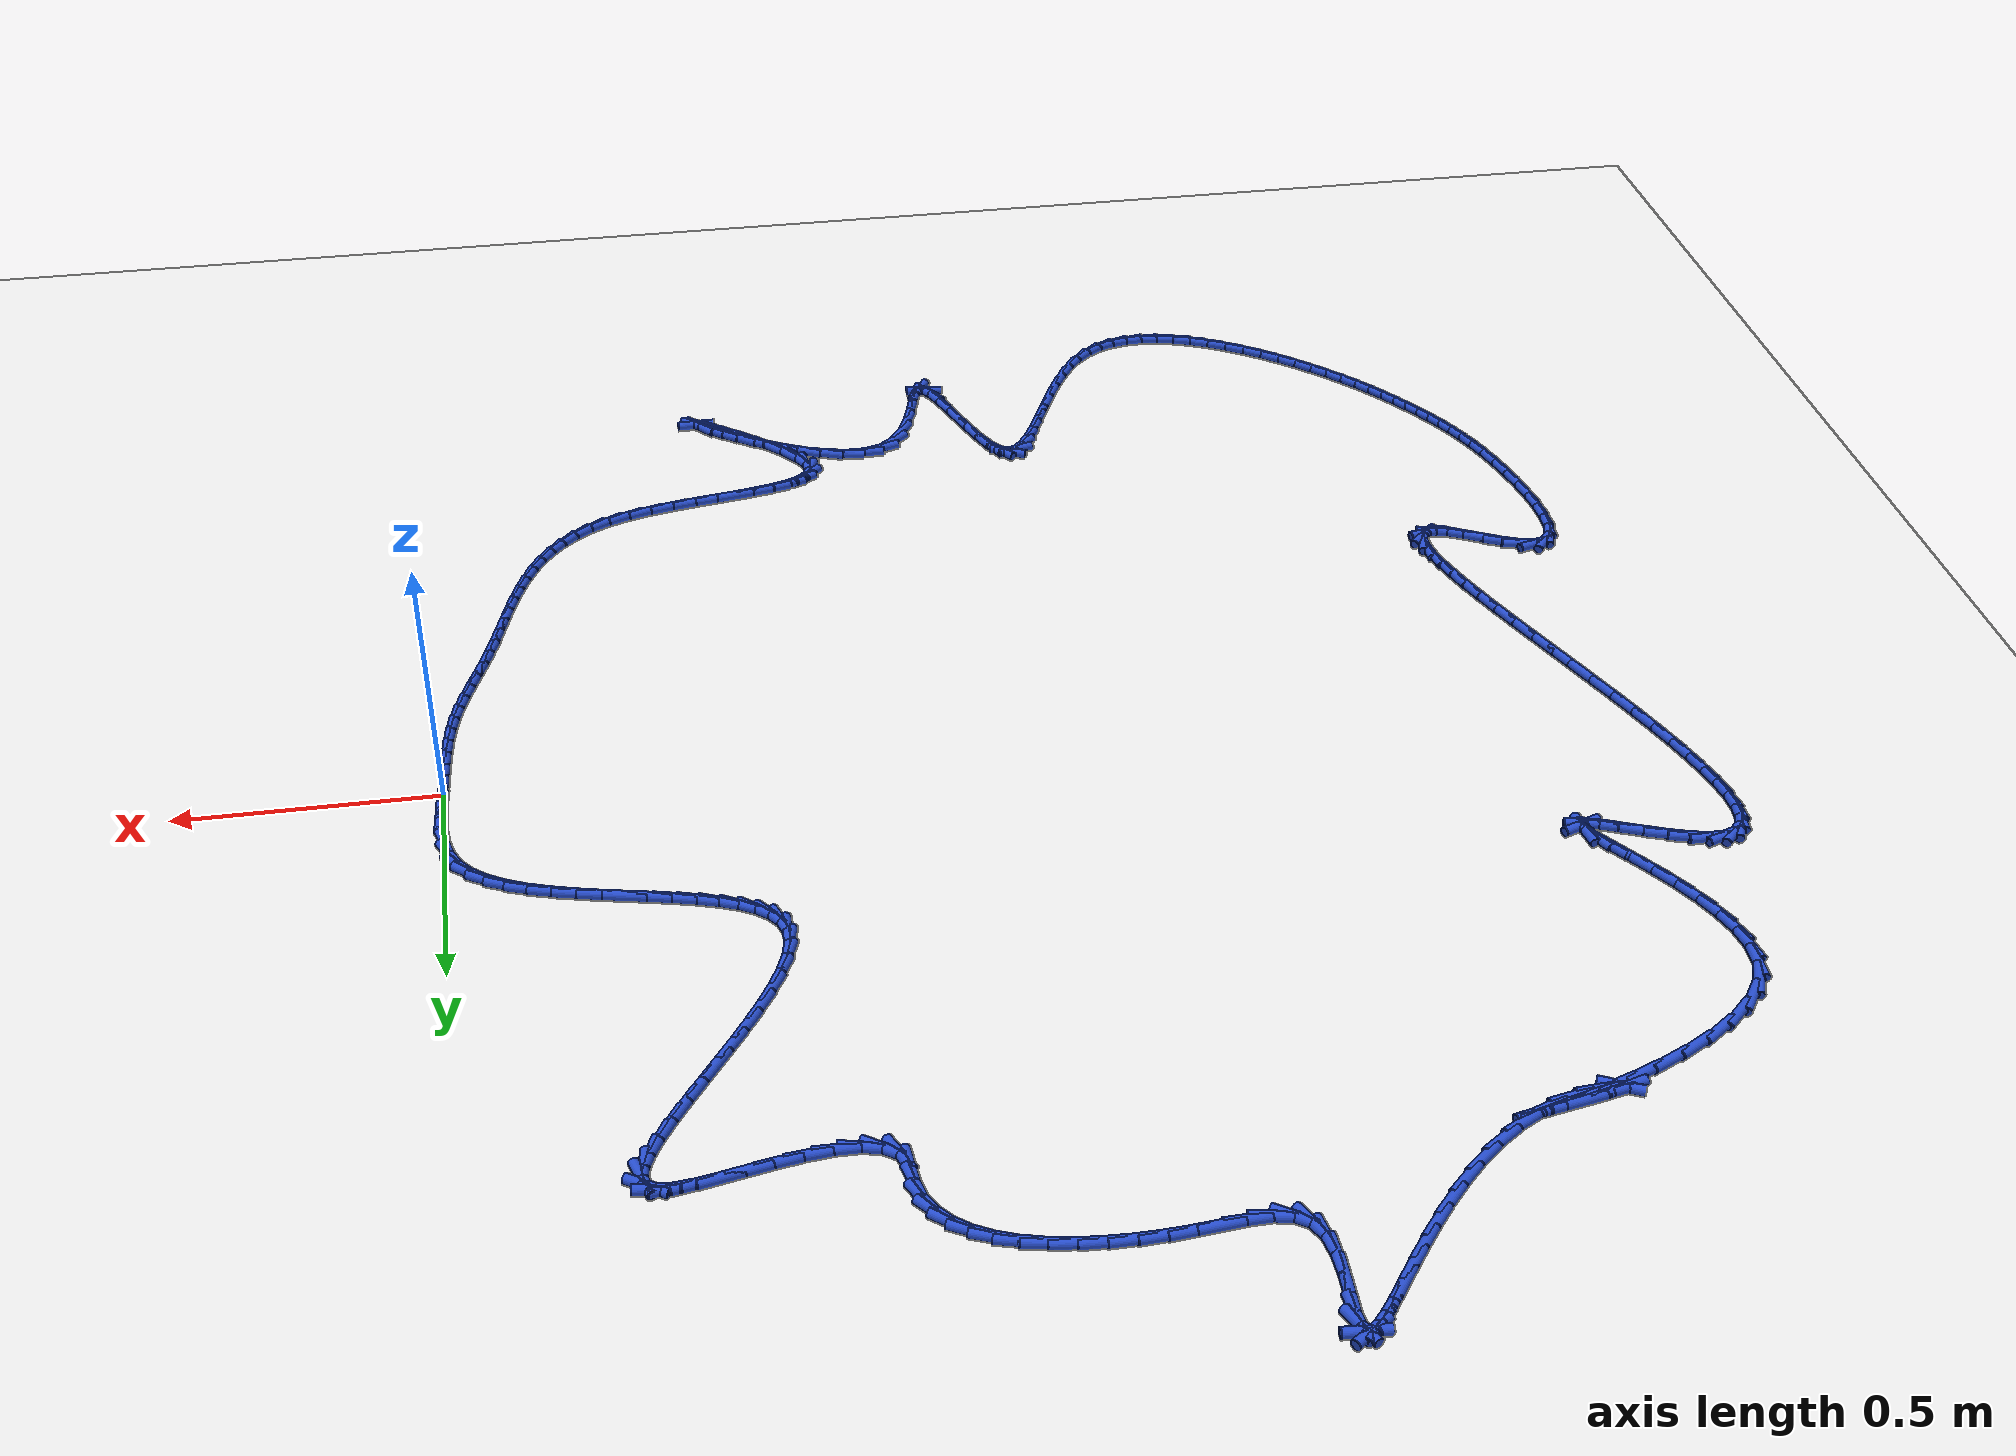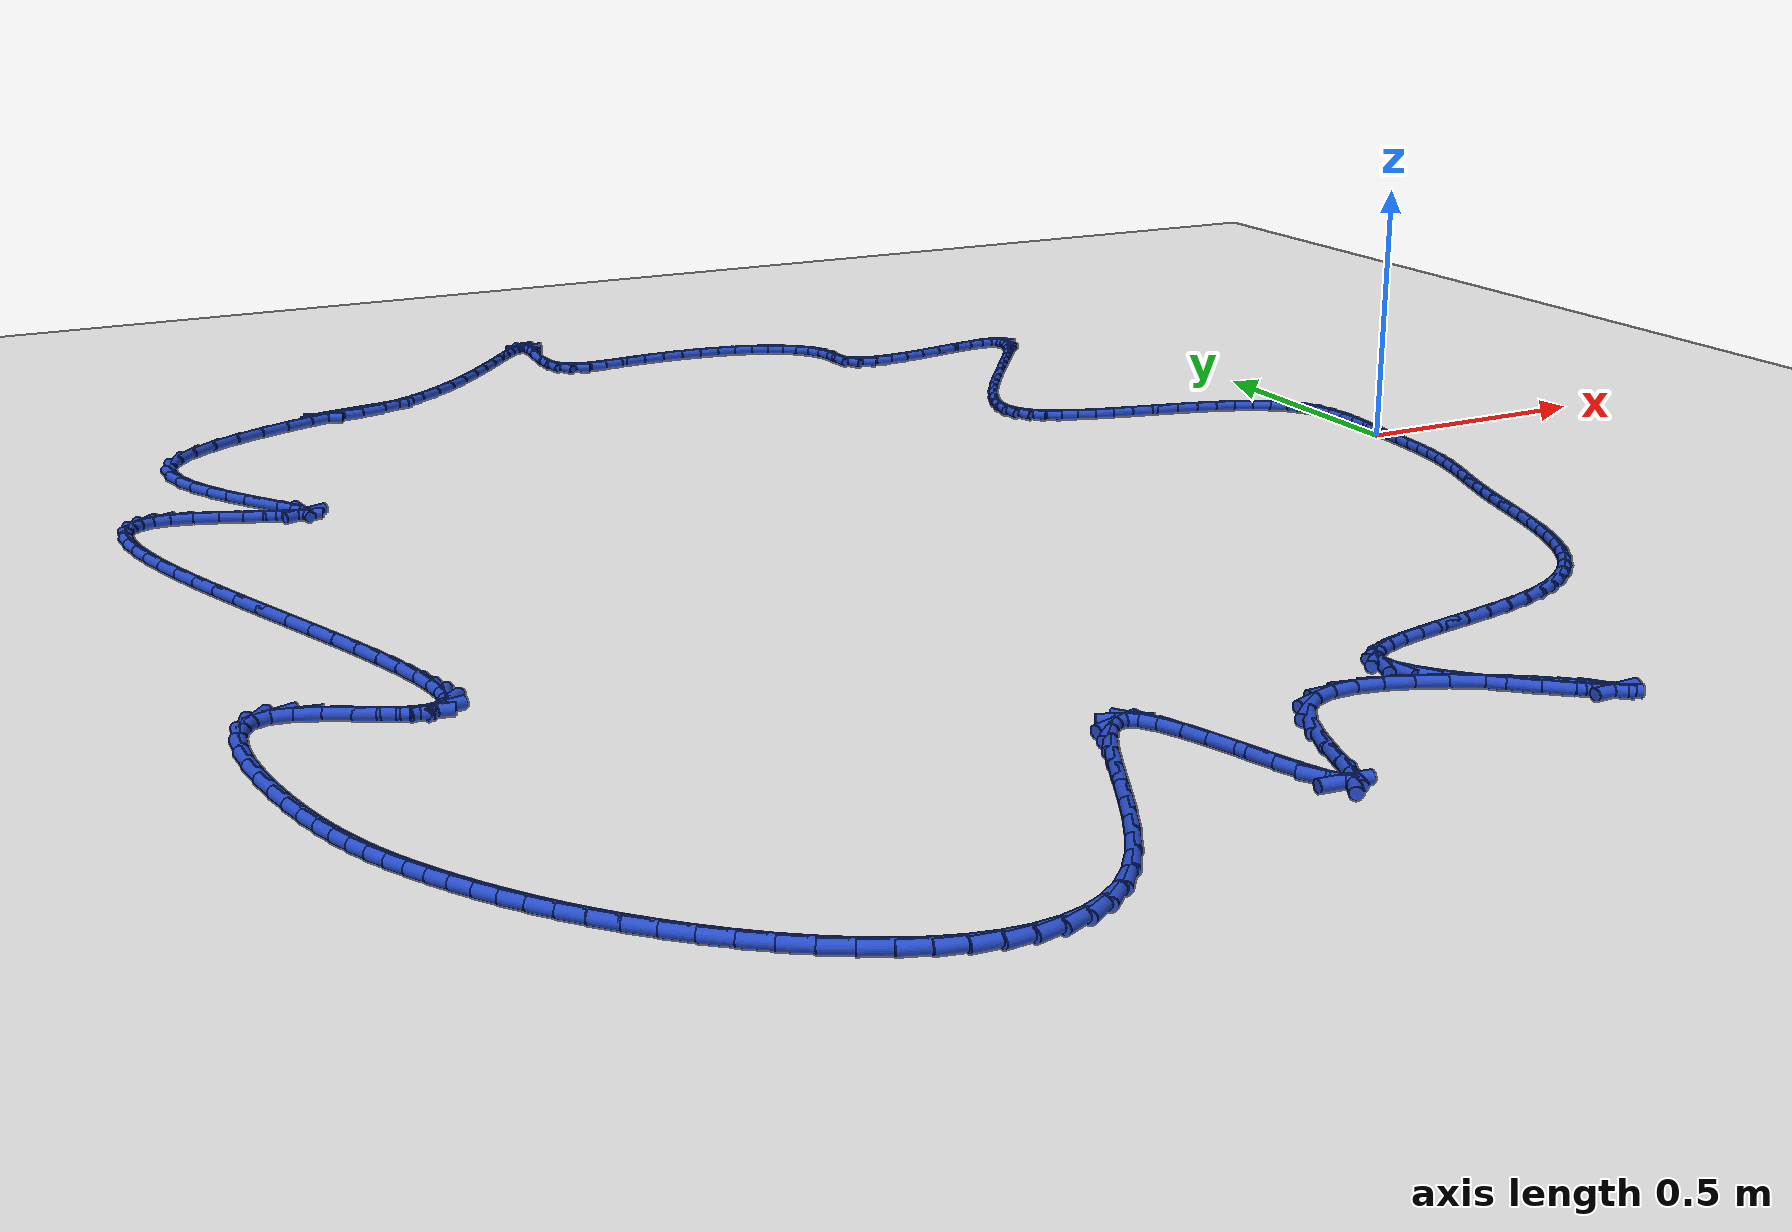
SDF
<sdf version="1.6">
 <world name="default">
  <light name="sun" type="directional">
   <pose>0 0 10 0 -0 0</pose>
   <diffuse>0.8 0.8 0.8 1</diffuse>
   <specular>0.2 0.2 0.2 1</specular>
   <attenuation>
    <range>1000</range>
    <constant>0.9</constant>
    <linear>0.01</linear>
    <quadratic>0.001</quadratic>
   </attenuation>
   <direction>-0.5 0.1 -0.9</direction>
  </light>
  <model name="ground_plane">
   <static>1</static>
   <link name="link">
    <collision name="collision">
     <geometry><plane><normal>0 0 1</normal><size>100 100</size></plane></geometry>
     <surface><friction><ode><mu>100</mu><mu2>50</mu2></ode></friction></surface>
    </collision>
    <visual name="visual">
     <cast_shadows>0</cast_shadows>
     <geometry><plane><normal>0 0 1</normal><size>100 100</size></plane></geometry>
     <material>
      <script><uri>file://media/materials/scripts/gazebo.material</uri><name>Gazebo/WhiteGlow</name></script>
     </material>
    </visual>
   </link>
  </model>
  <gravity>0 0 -9.8</gravity>
  <magnetic_field>6e-06 2.3e-05 -4.2e-05</magnetic_field>
  <atmosphere type="adiabatic"/>
  <physics name="default_physics" default="0" type="ode">
   <max_step_size>0.001</max_step_size>
   <real_time_factor>1</real_time_factor>
   <real_time_update_rate>1000</real_time_update_rate>
  </physics>
  <scene><ambient>0.4 0.4 0.4 1</ambient><background>0.7 0.7 0.7 1</background><shadows>1</shadows></scene>
  <spherical_coordinates>
   <surface_model>EARTH_WGS84</surface_model>
   <latitude_deg>0</latitude_deg>
   <longitude_deg>0</longitude_deg>
   <elevation>0</elevation>
   <heading_deg>0</heading_deg>
  </spherical_coordinates>
  <model name="line">
   <link name="link_0">
    <pose>2.42861286636753e-17 -9.71445146547012e-17 0.01 0 1.57 1.5118011852398148</pose>
    <collision name="collision">
     <geometry><cylinder><radius>0.01</radius><length>0.08</length></cylinder></geometry>
    </collision>
    <visual name="visual">
     <material>
      <script><name>Gazebo/Blue</name><uri>file://media/materials/scripts/gazebo.material</uri></script>
     </material>
     <geometry><cylinder><radius>0.01</radius><length>0.08</length></cylinder></geometry>
    </visual>
   </link>
   <link name="link_1">
    <pose>0.002303739772416932 0.03900433875733539 0.01 0 1.57 1.5351586536880117</pose>
    <collision name="collision">
     <geometry><cylinder><radius>0.01</radius><length>0.08</length></cylinder></geometry>
    </collision>
    <visual name="visual">
     <material>
      <script><name>Gazebo/Blue</name><uri>file://media/materials/scripts/gazebo.material</uri></script>
     </material>
     <geometry><cylinder><radius>0.01</radius><length>0.08</length></cylinder></geometry>
    </visual>
   </link>
   <link name="link_2">
    <pose>0.003697740250314615 0.07810370073165415 0.01 0 1.57 -1.5509076901935297</pose>
    <collision name="collision">
     <geometry><cylinder><radius>0.01</radius><length>0.08</length></cylinder></geometry>
    </collision>
    <visual name="visual">
     <material>
      <script><name>Gazebo/Blue</name><uri>file://media/materials/scripts/gazebo.material</uri></script>
     </material>
     <geometry><cylinder><radius>0.01</radius><length>0.08</length></cylinder></geometry>
    </visual>
   </link>
   <link name="link_3">
    <pose>0.002936328509903917 0.1163824102725819 0.01 0 1.57 -1.4573764426155094</pose>
    <collision name="collision">
     <geometry><cylinder><radius>0.01</radius><length>0.08</length></cylinder></geometry>
    </collision>
    <visual name="visual">
     <material>
      <script><name>Gazebo/Blue</name><uri>file://media/materials/scripts/gazebo.material</uri></script>
     </material>
     <geometry><cylinder><radius>0.01</radius><length>0.08</length></cylinder></geometry>
    </visual>
   </link>
   <link name="link_4">
    <pose>-0.001226168372604317 0.15292479172974435 0.01 0 1.57 -1.3164902696506535</pose>
    <collision name="collision">
     <geometry><cylinder><radius>0.01</radius><length>0.08</length></cylinder></geometry>
    </collision>
    <visual name="visual">
     <material>
      <script><name>Gazebo/Blue</name><uri>file://media/materials/scripts/gazebo.material</uri></script>
     </material>
     <geometry><cylinder><radius>0.01</radius><length>0.08</length></cylinder></geometry>
    </visual>
   </link>
   <link name="link_5">
    <pose>-0.010035423320999243 0.18681516945276722 0.01 0 1.57 -1.1193549788950194</pose>
    <collision name="collision">
     <geometry><cylinder><radius>0.01</radius><length>0.08</length></cylinder></geometry>
    </collision>
    <visual name="visual">
     <material>
      <script><name>Gazebo/Blue</name><uri>file://media/materials/scripts/gazebo.material</uri></script>
     </material>
     <geometry><cylinder><radius>0.01</radius><length>0.08</length></cylinder></geometry>
    </visual>
   </link>
   <link name="link_6">
    <pose>-0.024736949133175437 0.21713797354723255 0.01 0 1.57 -0.884915147896317</pose>
    <collision name="collision">
     <geometry><cylinder><radius>0.01</radius><length>0.08</length></cylinder></geometry>
    </collision>
    <visual name="visual">
     <material>
      <script><name>Gazebo/Blue</name><uri>file://media/materials/scripts/gazebo.material</uri></script>
     </material>
     <geometry><cylinder><radius>0.01</radius><length>0.08</length></cylinder></geometry>
    </visual>
   </link>
   <link name="link_7">
    <pose>-0.04612756798879818 0.24327397410493337 0.01 0 1.57 -0.6817286199915633</pose>
    <collision name="collision">
     <geometry><cylinder><radius>0.01</radius><length>0.08</length></cylinder></geometry>
    </collision>
    <visual name="visual">
     <material>
      <script><name>Gazebo/Blue</name><uri>file://media/materials/scripts/gazebo.material</uri></script>
     </material>
     <geometry><cylinder><radius>0.01</radius><length>0.08</length></cylinder></geometry>
    </visual>
   </link>
   <link name="link_8">
    <pose>-0.07357470376039342 0.2655479945528973 0.01 0 1.57 -0.5261334668051496</pose>
    <collision name="collision">
     <geometry><cylinder><radius>0.01</radius><length>0.08</length></cylinder></geometry>
    </collision>
    <visual name="visual">
     <material>
      <script><name>Gazebo/Blue</name><uri>file://media/materials/scripts/gazebo.material</uri></script>
     </material>
     <geometry><cylinder><radius>0.01</radius><length>0.08</length></cylinder></geometry>
    </visual>
   </link>
   <link name="link_9">
    <pose>-0.1061617666526671 0.2844724365802909 0.01 0 1.57 -0.4120162486994835</pose>
    <collision name="collision">
     <geometry><cylinder><radius>0.01</radius><length>0.08</length></cylinder></geometry>
    </collision>
    <visual name="visual">
     <material>
      <script><name>Gazebo/Blue</name><uri>file://media/materials/scripts/gazebo.material</uri></script>
     </material>
     <geometry><cylinder><radius>0.01</radius><length>0.08</length></cylinder></geometry>
    </visual>
   </link>
   <link name="link_10">
    <pose>-0.14297216687032516 0.30055970187628095 0.01 0 1.57 -0.33047666717313223</pose>
    <collision name="collision">
     <geometry><cylinder><radius>0.01</radius><length>0.08</length></cylinder></geometry>
    </collision>
    <visual name="visual">
     <material>
      <script><name>Gazebo/Blue</name><uri>file://media/materials/scripts/gazebo.material</uri></script>
     </material>
     <geometry><cylinder><radius>0.01</radius><length>0.08</length></cylinder></geometry>
    </visual>
   </link>
   <link name="link_11">
    <pose>-0.18308931461807346 0.31432219213003376 0.01 0 1.57 -0.27405707491371806</pose>
    <collision name="collision">
     <geometry><cylinder><radius>0.01</radius><length>0.08</length></cylinder></geometry>
    </collision>
    <visual name="visual">
     <material>
      <script><name>Gazebo/Blue</name><uri>file://media/materials/scripts/gazebo.material</uri></script>
     </material>
     <geometry><cylinder><radius>0.01</radius><length>0.08</length></cylinder></geometry>
    </visual>
   </link>
   <link name="link_12">
    <pose>-0.22559662010061804 0.3262723090307163 0.01 0 1.57 -0.23758068717680417</pose>
    <collision name="collision">
     <geometry><cylinder><radius>0.01</radius><length>0.08</length></cylinder></geometry>
    </collision>
    <visual name="visual">
     <material>
      <script><name>Gazebo/Blue</name><uri>file://media/materials/scripts/gazebo.material</uri></script>
     </material>
     <geometry><cylinder><radius>0.01</radius><length>0.08</length></cylinder></geometry>
    </visual>
   </link>
   <link name="link_13">
    <pose>-0.2695774935226647 0.336922454267495 0.01 0 1.57 -0.21792583812303976</pose>
    <collision name="collision">
     <geometry><cylinder><radius>0.01</radius><length>0.08</length></cylinder></geometry>
    </collision>
    <visual name="visual">
     <material>
      <script><name>Gazebo/Blue</name><uri>file://media/materials/scripts/gazebo.material</uri></script>
     </material>
     <geometry><cylinder><radius>0.01</radius><length>0.08</length></cylinder></geometry>
    </visual>
   </link>
   <link name="link_14">
    <pose>-0.3141153450889196 0.3467850295295366 0.01 0 1.57 -0.21370276437420313</pose>
    <collision name="collision">
     <geometry><cylinder><radius>0.01</radius><length>0.08</length></cylinder></geometry>
    </collision>
    <visual name="visual">
     <material>
      <script><name>Gazebo/Blue</name><uri>file://media/materials/scripts/gazebo.material</uri></script>
     </material>
     <geometry><cylinder><radius>0.01</radius><length>0.08</length></cylinder></geometry>
    </visual>
   </link>
   <link name="link_15">
    <pose>-0.35829358500408826 0.35637243650600753 0.01 0 1.57 -0.22512005235868032</pose>
    <collision name="collision">
     <geometry><cylinder><radius>0.01</radius><length>0.08</length></cylinder></geometry>
    </collision>
    <visual name="visual">
     <material>
      <script><name>Gazebo/Blue</name><uri>file://media/materials/scripts/gazebo.material</uri></script>
     </material>
     <geometry><cylinder><radius>0.01</radius><length>0.08</length></cylinder></geometry>
    </visual>
   </link>
   <link name="link_16">
    <pose>-0.4011956234728772 0.36619707688607467 0.01 0 1.57 -0.25413499040041554</pose>
    <collision name="collision">
     <geometry><cylinder><radius>0.01</radius><length>0.08</length></cylinder></geometry>
    </collision>
    <visual name="visual">
     <material>
      <script><name>Gazebo/Blue</name><uri>file://media/materials/scripts/gazebo.material</uri></script>
     </material>
     <geometry><cylinder><radius>0.01</radius><length>0.08</length></cylinder></geometry>
    </visual>
   </link>
   <link name="link_17">
    <pose>-0.4419048706999916 0.3767713523589043 0.01 0 1.57 -0.3049758280346327</pose>
    <collision name="collision">
     <geometry><cylinder><radius>0.01</radius><length>0.08</length></cylinder></geometry>
    </collision>
    <visual name="visual">
     <material>
      <script><name>Gazebo/Blue</name><uri>file://media/materials/scripts/gazebo.material</uri></script>
     </material>
     <geometry><cylinder><radius>0.01</radius><length>0.08</length></cylinder></geometry>
    </visual>
   </link>
   <link name="link_18">
    <pose>-0.4795047368901383 0.38860766461366353 0.01 0 1.57 -0.38515014080374577</pose>
    <collision name="collision">
     <geometry><cylinder><radius>0.01</radius><length>0.08</length></cylinder></geometry>
    </collision>
    <visual name="visual">
     <material>
      <script><name>Gazebo/Blue</name><uri>file://media/materials/scripts/gazebo.material</uri></script>
     </material>
     <geometry><cylinder><radius>0.01</radius><length>0.08</length></cylinder></geometry>
    </visual>
   </link>
   <link name="link_19">
    <pose>-0.5130786322480223 0.4022184153395184 0.01 0 1.57 -0.5068661121782086</pose>
    <collision name="collision">
     <geometry><cylinder><radius>0.01</radius><length>0.08</length></cylinder></geometry>
    </collision>
    <visual name="visual">
     <material>
      <script><name>Gazebo/Blue</name><uri>file://media/materials/scripts/gazebo.material</uri></script>
     </material>
     <geometry><cylinder><radius>0.01</radius><length>0.08</length></cylinder></geometry>
    </visual>
   </link>
   <link name="link_20">
    <pose>-0.5417099669783503 0.41811600622563616 0.01 0 1.57 -0.6874381057878393</pose>
    <collision name="collision">
     <geometry><cylinder><radius>0.01</radius><length>0.08</length></cylinder></geometry>
    </collision>
    <visual name="visual">
     <material>
      <script><name>Gazebo/Blue</name><uri>file://media/materials/scripts/gazebo.material</uri></script>
     </material>
     <geometry><cylinder><radius>0.01</radius><length>0.08</length></cylinder></geometry>
    </visual>
   </link>
   <link name="link_21">
    <pose>-0.5644821512858277 0.4368128389611829 0.01 0 1.57 -0.942288976830299</pose>
    <collision name="collision">
     <geometry><cylinder><radius>0.01</radius><length>0.08</length></cylinder></geometry>
    </collision>
    <visual name="visual">
     <material>
      <script><name>Gazebo/Blue</name><uri>file://media/materials/scripts/gazebo.material</uri></script>
     </material>
     <geometry><cylinder><radius>0.01</radius><length>0.08</length></cylinder></geometry>
    </visual>
   </link>
   <link name="link_22">
    <pose>-0.5804785953751608 0.45882131523532554 0.01 0 1.57 -1.2597698516216533</pose>
    <collision name="collision">
     <geometry><cylinder><radius>0.01</radius><length>0.08</length></cylinder></geometry>
    </collision>
    <visual name="visual">
     <material>
      <script><name>Gazebo/Blue</name><uri>file://media/materials/scripts/gazebo.material</uri></script>
     </material>
     <geometry><cylinder><radius>0.01</radius><length>0.08</length></cylinder></geometry>
    </visual>
   </link>
   <link name="link_23">
    <pose>-0.5887827094510554 0.4846538367372305 0.01 0 1.57 1.5678243590251086</pose>
    <collision name="collision">
     <geometry><cylinder><radius>0.01</radius><length>0.08</length></cylinder></geometry>
    </collision>
    <visual name="visual">
     <material>
      <script><name>Gazebo/Blue</name><uri>file://media/materials/scripts/gazebo.material</uri></script>
     </material>
     <geometry><cylinder><radius>0.01</radius><length>0.08</length></cylinder></geometry>
    </visual>
   </link>
   <link name="link_24">
    <pose>-0.5886934171412831 0.5146985928700692 0.01 0 1.57 1.3432820804817847</pose>
    <collision name="collision">
     <geometry><cylinder><radius>0.01</radius><length>0.08</length></cylinder></geometry>
    </collision>
    <visual name="visual">
     <material>
      <script><name>Gazebo/Blue</name><uri>file://media/materials/scripts/gazebo.material</uri></script>
     </material>
     <geometry><cylinder><radius>0.01</radius><length>0.08</length></cylinder></geometry>
    </visual>
   </link>
   <link name="link_25">
    <pose>-0.5808512956897186 0.5485705039742337 0.01 0 1.57 1.1988853763341873</pose>
    <collision name="collision">
     <geometry><cylinder><radius>0.01</radius><length>0.08</length></cylinder></geometry>
    </collision>
    <visual name="visual">
     <material>
      <script><name>Gazebo/Blue</name><uri>file://media/materials/scripts/gazebo.material</uri></script>
     </material>
     <geometry><cylinder><radius>0.01</radius><length>0.08</length></cylinder></geometry>
    </visual>
   </link>
   <link name="link_26">
    <pose>-0.5664123599053182 0.5855874152597788 0.01 0 1.57 1.1043340571011162</pose>
    <collision name="collision">
     <geometry><cylinder><radius>0.01</radius><length>0.08</length></cylinder></geometry>
    </collision>
    <visual name="visual">
     <material>
      <script><name>Gazebo/Blue</name><uri>file://media/materials/scripts/gazebo.material</uri></script>
     </material>
     <geometry><cylinder><radius>0.01</radius><length>0.08</length></cylinder></geometry>
    </visual>
   </link>
   <link name="link_27">
    <pose>-0.5465336927912743 0.6250665562774373 0.01 0 1.57 1.041027317721969</pose>
    <collision name="collision">
     <geometry><cylinder><radius>0.01</radius><length>0.08</length></cylinder></geometry>
    </collision>
    <visual name="visual">
     <material>
      <script><name>Gazebo/Blue</name><uri>file://media/materials/scripts/gazebo.material</uri></script>
     </material>
     <geometry><cylinder><radius>0.01</radius><length>0.08</length></cylinder></geometry>
    </visual>
   </link>
   <link name="link_28">
    <pose>-0.522372377350779 0.6663251565779423 0.01 0 1.57 0.9984824920722688</pose>
    <collision name="collision">
     <geometry><cylinder><radius>0.01</radius><length>0.08</length></cylinder></geometry>
    </collision>
    <visual name="visual">
     <material>
      <script><name>Gazebo/Blue</name><uri>file://media/materials/scripts/gazebo.material</uri></script>
     </material>
     <geometry><cylinder><radius>0.01</radius><length>0.08</length></cylinder></geometry>
    </visual>
   </link>
   <link name="link_29">
    <pose>-0.49508549658702483 0.708680445712026 0.01 0 1.57 0.9708700088170761</pose>
    <collision name="collision">
     <geometry><cylinder><radius>0.01</radius><length>0.08</length></cylinder></geometry>
    </collision>
    <visual name="visual">
     <material>
      <script><name>Gazebo/Blue</name><uri>file://media/materials/scripts/gazebo.material</uri></script>
     </material>
     <geometry><cylinder><radius>0.01</radius><length>0.08</length></cylinder></geometry>
    </visual>
   </link>
   <link name="link_30">
    <pose>-0.46583013350320435 0.751449653230421 0.01 0 1.57 0.9550896312616892</pose>
    <collision name="collision">
     <geometry><cylinder><radius>0.01</radius><length>0.08</length></cylinder></geometry>
    </collision>
    <visual name="visual">
     <material>
      <script><name>Gazebo/Blue</name><uri>file://media/materials/scripts/gazebo.material</uri></script>
     </material>
     <geometry><cylinder><radius>0.01</radius><length>0.08</length></cylinder></geometry>
    </visual>
   </link>
   <link name="link_31">
    <pose>-0.4357633711025099 0.7939500086838602 0.01 0 1.57 0.9498553203666651</pose>
    <collision name="collision">
     <geometry><cylinder><radius>0.01</radius><length>0.08</length></cylinder></geometry>
    </collision>
    <visual name="visual">
     <material>
      <script><name>Gazebo/Blue</name><uri>file://media/materials/scripts/gazebo.material</uri></script>
     </material>
     <geometry><cylinder><radius>0.01</radius><length>0.08</length></cylinder></geometry>
    </visual>
   </link>
   <link name="link_32">
    <pose>-0.4060422923881338 0.8354987416230766 0.01 0 1.57 0.9554066238966101</pose>
    <collision name="collision">
     <geometry><cylinder><radius>0.01</radius><length>0.08</length></cylinder></geometry>
    </collision>
    <visual name="visual">
     <material>
      <script><name>Gazebo/Blue</name><uri>file://media/materials/scripts/gazebo.material</uri></script>
     </material>
     <geometry><cylinder><radius>0.01</radius><length>0.08</length></cylinder></geometry>
    </visual>
   </link>
   <link name="link_33">
    <pose>-0.3778239803632683 0.8754130815988024 0.01 0 1.57 0.9737582310132793</pose>
    <collision name="collision">
     <geometry><cylinder><radius>0.01</radius><length>0.08</length></cylinder></geometry>
    </collision>
    <visual name="visual">
     <material>
      <script><name>Gazebo/Blue</name><uri>file://media/materials/scripts/gazebo.material</uri></script>
     </material>
     <geometry><cylinder><radius>0.01</radius><length>0.08</length></cylinder></geometry>
    </visual>
   </link>
   <link name="link_34">
    <pose>-0.35226551803110623 0.9130102581617702 0.01 0 1.57 1.0097429075592725</pose>
    <collision name="collision">
     <geometry><cylinder><radius>0.01</radius><length>0.08</length></cylinder></geometry>
    </collision>
    <visual name="visual">
     <material>
      <script><name>Gazebo/Blue</name><uri>file://media/materials/scripts/gazebo.material</uri></script>
     </material>
     <geometry><cylinder><radius>0.01</radius><length>0.08</length></cylinder></geometry>
    </visual>
   </link>
   <link name="link_35">
    <pose>-0.3305239883948398 0.947607500862713 0.01 0 1.57 1.0738200567240912</pose>
    <collision name="collision">
     <geometry><cylinder><radius>0.01</radius><length>0.08</length></cylinder></geometry>
    </collision>
    <visual name="visual">
     <material>
      <script><name>Gazebo/Blue</name><uri>file://media/materials/scripts/gazebo.material</uri></script>
     </material>
     <geometry><cylinder><radius>0.01</radius><length>0.08</length></cylinder></geometry>
    </visual>
   </link>
   <link name="link_36">
    <pose>-0.3137564744576612 0.9785220392523635 0.01 0 1.57 1.189744891137479</pose>
    <collision name="collision">
     <geometry><cylinder><radius>0.01</radius><length>0.08</length></cylinder></geometry>
    </collision>
    <visual name="visual">
     <material>
      <script><name>Gazebo/Blue</name><uri>file://media/materials/scripts/gazebo.material</uri></script>
     </material>
     <geometry><cylinder><radius>0.01</radius><length>0.08</length></cylinder></geometry>
    </visual>
   </link>
   <link name="link_37">
    <pose>-0.3031200592227631 1.005071102881454 0.01 0 1.57 1.4163112702088512</pose>
    <collision name="collision">
     <geometry><cylinder><radius>0.01</radius><length>0.08</length></cylinder></geometry>
    </collision>
    <visual name="visual">
     <material>
      <script><name>Gazebo/Blue</name><uri>file://media/materials/scripts/gazebo.material</uri></script>
     </material>
     <geometry><cylinder><radius>0.01</radius><length>0.08</length></cylinder></geometry>
    </visual>
   </link>
   <link name="link_38">
    <pose>-0.2997718256933378 1.0265719213007176 0.01 0 1.57 -1.258180067983915</pose>
    <collision name="collision">
     <geometry><cylinder><radius>0.01</radius><length>0.08</length></cylinder></geometry>
    </collision>
    <visual name="visual">
     <material>
      <script><name>Gazebo/Blue</name><uri>file://media/materials/scripts/gazebo.material</uri></script>
     </material>
     <geometry><cylinder><radius>0.01</radius><length>0.08</length></cylinder></geometry>
    </visual>
   </link>
   <link name="link_39">
    <pose>-0.3048688568725777 1.0423417240608868 0.01 0 1.57 -0.566819588395032</pose>
    <collision name="collision">
     <geometry><cylinder><radius>0.01</radius><length>0.08</length></cylinder></geometry>
    </collision>
    <visual name="visual">
     <material>
      <script><name>Gazebo/Blue</name><uri>file://media/materials/scripts/gazebo.material</uri></script>
     </material>
     <geometry><cylinder><radius>0.01</radius><length>0.08</length></cylinder></geometry>
    </visual>
   </link>
   <link name="link_40">
    <pose>-0.31956823576367516 1.0516977407126944 0.01 0 1.57 -0.09737909518424188</pose>
    <collision name="collision">
     <geometry><cylinder><radius>0.01</radius><length>0.08</length></cylinder></geometry>
    </collision>
    <visual name="visual">
     <material>
      <script><name>Gazebo/Blue</name><uri>file://media/materials/scripts/gazebo.material</uri></script>
     </material>
     <geometry><cylinder><radius>0.01</radius><length>0.08</length></cylinder></geometry>
    </visual>
   </link>
   <link name="link_41">
    <pose>-0.3447503156409448 1.0541577295551623 0.01 0 1.57 0.0969121332372446</pose>
    <collision name="collision">
     <geometry><cylinder><radius>0.01</radius><length>0.08</length></cylinder></geometry>
    </collision>
    <visual name="visual">
     <material>
      <script><name>Gazebo/Blue</name><uri>file://media/materials/scripts/gazebo.material</uri></script>
     </material>
     <geometry><cylinder><radius>0.01</radius><length>0.08</length></cylinder></geometry>
    </visual>
   </link>
   <link name="link_42">
    <pose>-0.3791191048341386 1.0508165101208444 0.01 0 1.57 0.17528033534081366</pose>
    <collision name="collision">
     <geometry><cylinder><radius>0.01</radius><length>0.08</length></cylinder></geometry>
    </collision>
    <visual name="visual">
     <material>
      <script><name>Gazebo/Blue</name><uri>file://media/materials/scripts/gazebo.material</uri></script>
     </material>
     <geometry><cylinder><radius>0.01</radius><length>0.08</length></cylinder></geometry>
    </visual>
   </link>
   <link name="link_43">
    <pose>-0.4203493797817771 1.0435147220017615 0.01 0 1.57 0.20296171793397277</pose>
    <collision name="collision">
     <geometry><cylinder><radius>0.01</radius><length>0.08</length></cylinder></geometry>
    </collision>
    <visual name="visual">
     <material>
      <script><name>Gazebo/Blue</name><uri>file://media/materials/scripts/gazebo.material</uri></script>
     </material>
     <geometry><cylinder><radius>0.01</radius><length>0.08</length></cylinder></geometry>
    </visual>
   </link>
   <link name="link_44">
    <pose>-0.4661097912672229 1.0340974436695838 0.01 0 1.57 0.19931653104934366</pose>
    <collision name="collision">
     <geometry><cylinder><radius>0.01</radius><length>0.08</length></cylinder></geometry>
    </collision>
    <visual name="visual">
     <material>
      <script><name>Gazebo/Blue</name><uri>file://media/materials/scripts/gazebo.material</uri></script>
     </material>
     <geometry><cylinder><radius>0.01</radius><length>0.08</length></cylinder></geometry>
    </visual>
   </link>
   <link name="link_45">
    <pose>-0.5140689900738379 1.0244097535959797 0.01 0 1.57 0.16803440817700285</pose>
    <collision name="collision">
     <geometry><cylinder><radius>0.01</radius><length>0.08</length></cylinder></geometry>
    </collision>
    <visual name="visual">
     <material>
      <script><name>Gazebo/Blue</name><uri>file://media/materials/scripts/gazebo.material</uri></script>
     </material>
     <geometry><cylinder><radius>0.01</radius><length>0.08</length></cylinder></geometry>
    </visual>
   </link>
   <link name="link_46">
    <pose>-0.5618956269849832 1.0162967302526178 0.01 0 1.57 0.10309431062793215</pose>
    <collision name="collision">
     <geometry><cylinder><radius>0.01</radius><length>0.08</length></cylinder></geometry>
    </collision>
    <visual name="visual">
     <material>
      <script><name>Gazebo/Blue</name><uri>file://media/materials/scripts/gazebo.material</uri></script>
     </material>
     <geometry><cylinder><radius>0.01</radius><length>0.08</length></cylinder></geometry>
    </visual>
   </link>
   <link name="link_47">
    <pose>-0.6072583527840224 1.011603452111168 0.01 0 1.57 -0.014087834031935654</pose>
    <collision name="collision">
     <geometry><cylinder><radius>0.01</radius><length>0.08</length></cylinder></geometry>
    </collision>
    <visual name="visual">
     <material>
      <script><name>Gazebo/Blue</name><uri>file://media/materials/scripts/gazebo.material</uri></script>
     </material>
     <geometry><cylinder><radius>0.01</radius><length>0.08</length></cylinder></geometry>
    </visual>
   </link>
   <link name="link_48">
    <pose>-0.6478258182543162 1.0121749976432988 0.01 0 1.57 -0.22578580161414125</pose>
    <collision name="collision">
     <geometry><cylinder><radius>0.01</radius><length>0.08</length></cylinder></geometry>
    </collision>
    <visual name="visual">
     <material>
      <script><name>Gazebo/Blue</name><uri>file://media/materials/scripts/gazebo.material</uri></script>
     </material>
     <geometry><cylinder><radius>0.01</radius><length>0.08</length></cylinder></geometry>
    </visual>
   </link>
   <link name="link_49">
    <pose>-0.6812666741792269 1.0198564453206793 0.01 0 1.57 -0.60647096507086</pose>
    <collision name="collision">
     <geometry><cylinder><radius>0.01</radius><length>0.08</length></cylinder></geometry>
    </collision>
    <visual name="visual">
     <material>
      <script><name>Gazebo/Blue</name><uri>file://media/materials/scripts/gazebo.material</uri></script>
     </material>
     <geometry><cylinder><radius>0.01</radius><length>0.08</length></cylinder></geometry>
    </visual>
   </link>
   <link name="link_50">
    <pose>-0.705249571342117 1.0364928736149794 0.01 0 1.57 -1.152584315193605</pose>
    <collision name="collision">
     <geometry><cylinder><radius>0.01</radius><length>0.08</length></cylinder></geometry>
    </collision>
    <visual name="visual">
     <material>
      <script><name>Gazebo/Blue</name><uri>file://media/materials/scripts/gazebo.material</uri></script>
     </material>
     <geometry><cylinder><radius>0.01</radius><length>0.08</length></cylinder></geometry>
    </visual>
   </link>
   <link name="link_51">
    <pose>-0.7174431608896911 1.0639293607119844 0.01 0 1.57 -1.4970216193585513</pose>
    <collision name="collision">
     <geometry><cylinder><radius>0.01</radius><length>0.08</length></cylinder></geometry>
    </collision>
    <visual name="visual">
     <material>
      <script><name>Gazebo/Blue</name><uri>file://media/materials/scripts/gazebo.material</uri></script>
     </material>
     <geometry><cylinder><radius>0.01</radius><length>0.08</length></cylinder></geometry>
    </visual>
   </link>
   <link name="link_52">
    <pose>-0.7201368327279122 1.1003752268032798 0.01 0 1.57 -1.349104011074392</pose>
    <collision name="collision">
     <geometry><cylinder><radius>0.01</radius><length>0.08</length></cylinder></geometry>
    </collision>
    <visual name="visual">
     <material>
      <script><name>Gazebo/Blue</name><uri>file://media/materials/scripts/gazebo.material</uri></script>
     </material>
     <geometry><cylinder><radius>0.01</radius><length>0.08</length></cylinder></geometry>
    </visual>
   </link>
   <link name="link_53">
    <pose>-0.7278001419012158 1.1343743834724014 0.01 0 1.57 -1.106657936353359</pose>
    <collision name="collision">
     <geometry><cylinder><radius>0.01</radius><length>0.08</length></cylinder></geometry>
    </collision>
    <visual name="visual">
     <material>
      <script><name>Gazebo/Blue</name><uri>file://media/materials/scripts/gazebo.material</uri></script>
     </material>
     <geometry><cylinder><radius>0.01</radius><length>0.08</length></cylinder></geometry>
    </visual>
   </link>
   <link name="link_54">
    <pose>-0.7425952766973491 1.1639283827754703 0.01 0 1.57 -0.8736379032597319</pose>
    <collision name="collision">
     <geometry><cylinder><radius>0.01</radius><length>0.08</length></cylinder></geometry>
    </collision>
    <visual name="visual">
     <material>
      <script><name>Gazebo/Blue</name><uri>file://media/materials/scripts/gazebo.material</uri></script>
     </material>
     <geometry><cylinder><radius>0.01</radius><length>0.08</length></cylinder></geometry>
    </visual>
   </link>
   <link name="link_55">
    <pose>-0.7638103331912425 1.1892615348091882 0.01 0 1.57 -0.670152802200831</pose>
    <collision name="collision">
     <geometry><cylinder><radius>0.01</radius><length>0.08</length></cylinder></geometry>
    </collision>
    <visual name="visual">
     <material>
      <script><name>Gazebo/Blue</name><uri>file://media/materials/scripts/gazebo.material</uri></script>
     </material>
     <geometry><cylinder><radius>0.01</radius><length>0.08</length></cylinder></geometry>
    </visual>
   </link>
   <link name="link_56">
    <pose>-0.7907334074578248 1.210598149670255 0.01 0 1.57 -0.5030556786254259</pose>
    <collision name="collision">
     <geometry><cylinder><radius>0.01</radius><length>0.08</length></cylinder></geometry>
    </collision>
    <visual name="visual">
     <material>
      <script><name>Gazebo/Blue</name><uri>file://media/materials/scripts/gazebo.material</uri></script>
     </material>
     <geometry><cylinder><radius>0.01</radius><length>0.08</length></cylinder></geometry>
    </visual>
   </link>
   <link name="link_57">
    <pose>-0.8226525955720265 1.228162537455373 0.01 0 1.57 -0.3693877594784987</pose>
    <collision name="collision">
     <geometry><cylinder><radius>0.01</radius><length>0.08</length></cylinder></geometry>
    </collision>
    <visual name="visual">
     <material>
      <script><name>Gazebo/Blue</name><uri>file://media/materials/scripts/gazebo.material</uri></script>
     </material>
     <geometry><cylinder><radius>0.01</radius><length>0.08</length></cylinder></geometry>
    </visual>
   </link>
   <link name="link_58">
    <pose>-0.8588559936087773 1.242179008261243 0.01 0 1.57 -0.2626201064883704</pose>
    <collision name="collision">
     <geometry><cylinder><radius>0.01</radius><length>0.08</length></cylinder></geometry>
    </collision>
    <visual name="visual">
     <material>
      <script><name>Gazebo/Blue</name><uri>file://media/materials/scripts/gazebo.material</uri></script>
     </material>
     <geometry><cylinder><radius>0.01</radius><length>0.08</length></cylinder></geometry>
    </visual>
   </link>
   <link name="link_59">
    <pose>-0.8986316976430062 1.252871872184565 0.01 0 1.57 -0.17625370077584482</pose>
    <collision name="collision">
     <geometry><cylinder><radius>0.01</radius><length>0.08</length></cylinder></geometry>
    </collision>
    <visual name="visual">
     <material>
      <script><name>Gazebo/Blue</name><uri>file://media/materials/scripts/gazebo.material</uri></script>
     </material>
     <geometry><cylinder><radius>0.01</radius><length>0.08</length></cylinder></geometry>
    </visual>
   </link>
   <link name="link_60">
    <pose>-0.9412678037496439 1.2604654393220416 0.01 0 1.57 -0.10497436481510176</pose>
    <collision name="collision">
     <geometry><cylinder><radius>0.01</radius><length>0.08</length></cylinder></geometry>
    </collision>
    <visual name="visual">
     <material>
      <script><name>Gazebo/Blue</name><uri>file://media/materials/scripts/gazebo.material</uri></script>
     </material>
     <geometry><cylinder><radius>0.01</radius><length>0.08</length></cylinder></geometry>
    </visual>
   </link>
   <link name="link_61">
    <pose>-0.9860524080036196 1.265184019770373 0.01 0 1.57 -0.044709481147856237</pose>
    <collision name="collision">
     <geometry><cylinder><radius>0.01</radius><length>0.08</length></cylinder></geometry>
    </collision>
    <visual name="visual">
     <material>
      <script><name>Gazebo/Blue</name><uri>file://media/materials/scripts/gazebo.material</uri></script>
     </material>
     <geometry><cylinder><radius>0.01</radius><length>0.08</length></cylinder></geometry>
    </visual>
   </link>
   <link name="link_62">
    <pose>-1.0322736064798628 1.2672519236262603 0.01 0 1.57 0.007635507239381281</pose>
    <collision name="collision">
     <geometry><cylinder><radius>0.01</radius><length>0.08</length></cylinder></geometry>
    </collision>
    <visual name="visual">
     <material>
      <script><name>Gazebo/Blue</name><uri>file://media/materials/scripts/gazebo.material</uri></script>
     </material>
     <geometry><cylinder><radius>0.01</radius><length>0.08</length></cylinder></geometry>
    </visual>
   </link>
   <link name="link_63">
    <pose>-1.0792194952533036 1.2668934609864044 0.01 0 1.57 0.05447312774394662</pose>
    <collision name="collision">
     <geometry><cylinder><radius>0.01</radius><length>0.08</length></cylinder></geometry>
    </collision>
    <visual name="visual">
     <material>
      <script><name>Gazebo/Blue</name><uri>file://media/materials/scripts/gazebo.material</uri></script>
     </material>
     <geometry><cylinder><radius>0.01</radius><length>0.08</length></cylinder></geometry>
    </visual>
   </link>
   <link name="link_64">
    <pose>-1.126178170398872 1.2643329419475071 0.01 0 1.57 0.09641894953253058</pose>
    <collision name="collision">
     <geometry><cylinder><radius>0.01</radius><length>0.08</length></cylinder></geometry>
    </collision>
    <visual name="visual">
     <material>
      <script><name>Gazebo/Blue</name><uri>file://media/materials/scripts/gazebo.material</uri></script>
     </material>
     <geometry><cylinder><radius>0.01</radius><length>0.08</length></cylinder></geometry>
    </visual>
   </link>
   <link name="link_65">
    <pose>-1.1724070931663644 1.259861733481744 0.01 0 1.57 0.10208965063162351</pose>
    <collision name="collision">
     <geometry><cylinder><radius>0.01</radius><length>0.08</length></cylinder></geometry>
    </collision>
    <visual name="visual">
     <material>
      <script><name>Gazebo/Blue</name><uri>file://media/materials/scripts/gazebo.material</uri></script>
     </material>
     <geometry><cylinder><radius>0.01</radius><length>0.08</length></cylinder></geometry>
    </visual>
   </link>
   <link name="link_66">
    <pose>-1.2164422162572017 1.2553505198471393 0.01 0 1.57 0.02724372632855227</pose>
    <collision name="collision">
     <geometry><cylinder><radius>0.01</radius><length>0.08</length></cylinder></geometry>
    </collision>
    <visual name="visual">
     <material>
      <script><name>Gazebo/Blue</name><uri>file://media/materials/scripts/gazebo.material</uri></script>
     </material>
     <geometry><cylinder><radius>0.01</radius><length>0.08</length></cylinder></geometry>
    </visual>
   </link>
   <link name="link_67">
    <pose>-1.2560884638192504 1.2542701410222292 0.01 0 1.57 -0.17654307387412205</pose>
    <collision name="collision">
     <geometry><cylinder><radius>0.01</radius><length>0.08</length></cylinder></geometry>
    </collision>
    <visual name="visual">
     <material>
      <script><name>Gazebo/Blue</name><uri>file://media/materials/scripts/gazebo.material</uri></script>
     </material>
     <geometry><cylinder><radius>0.01</radius><length>0.08</length></cylinder></geometry>
    </visual>
   </link>
   <link name="link_68">
    <pose>-1.289118221071649 1.2601626617724484 0.01 0 1.57 -0.5960800152873245</pose>
    <collision name="collision">
     <geometry><cylinder><radius>0.01</radius><length>0.08</length></cylinder></geometry>
    </collision>
    <visual name="visual">
     <material>
      <script><name>Gazebo/Blue</name><uri>file://media/materials/scripts/gazebo.material</uri></script>
     </material>
     <geometry><cylinder><radius>0.01</radius><length>0.08</length></cylinder></geometry>
    </visual>
   </link>
   <link name="link_69">
    <pose>-1.3133038732335354 1.2765701468632322 0.01 0 1.57 -1.1235835575818764</pose>
    <collision name="collision">
     <geometry><cylinder><radius>0.01</radius><length>0.08</length></cylinder></geometry>
    </collision>
    <visual name="visual">
     <material>
      <script><name>Gazebo/Blue</name><uri>file://media/materials/scripts/gazebo.material</uri></script>
     </material>
     <geometry><cylinder><radius>0.01</radius><length>0.08</length></cylinder></geometry>
    </visual>
   </link>
   <link name="link_70">
    <pose>-1.3272426584791428 1.3056321649214335 0.01 0 1.57 -1.4221722611407408</pose>
    <collision name="collision">
     <geometry><cylinder><radius>0.01</radius><length>0.08</length></cylinder></geometry>
    </collision>
    <visual name="visual">
     <material>
      <script><name>Gazebo/Blue</name><uri>file://media/materials/scripts/gazebo.material</uri></script>
     </material>
     <geometry><cylinder><radius>0.01</radius><length>0.08</length></cylinder></geometry>
    </visual>
   </link>
   <link name="link_71">
    <pose>-1.332941187362738 1.3436913342587757 0.01 0 1.57 -1.5625479537765008</pose>
    <collision name="collision">
     <geometry><cylinder><radius>0.01</radius><length>0.08</length></cylinder></geometry>
    </collision>
    <visual name="visual">
     <material>
      <script><name>Gazebo/Blue</name><uri>file://media/materials/scripts/gazebo.material</uri></script>
     </material>
     <geometry><cylinder><radius>0.01</radius><length>0.08</length></cylinder></geometry>
    </visual>
   </link>
   <link name="link_72">
    <pose>-1.333286813682387 1.3855927468813718 0.01 0 1.57 1.5186144525834042</pose>
    <collision name="collision">
     <geometry><cylinder><radius>0.01</radius><length>0.08</length></cylinder></geometry>
    </collision>
    <visual name="visual">
     <material>
      <script><name>Gazebo/Blue</name><uri>file://media/materials/scripts/gazebo.material</uri></script>
     </material>
     <geometry><cylinder><radius>0.01</radius><length>0.08</length></cylinder></geometry>
    </visual>
   </link>
   <link name="link_73">
    <pose>-1.3311668923484643 1.426181492904086 0.01 0 1.57 1.5210701822027162</pose>
    <collision name="collision">
     <geometry><cylinder><radius>0.01</radius><length>0.08</length></cylinder></geometry>
    </collision>
    <visual name="visual">
     <material>
      <script><name>Gazebo/Blue</name><uri>file://media/materials/scripts/gazebo.material</uri></script>
     </material>
     <geometry><cylinder><radius>0.01</radius><length>0.08</length></cylinder></geometry>
    </visual>
   </link>
   <link name="link_74">
    <pose>-1.329468778271342 1.4603026624417823 0.01 0 1.57 -1.510640885980615</pose>
    <collision name="collision">
     <geometry><cylinder><radius>0.01</radius><length>0.08</length></cylinder></geometry>
    </collision>
    <visual name="visual">
     <material>
      <script><name>Gazebo/Blue</name><uri>file://media/materials/scripts/gazebo.material</uri></script>
     </material>
     <geometry><cylinder><radius>0.01</radius><length>0.08</length></cylinder></geometry>
    </visual>
   </link>
   <link name="link_75">
    <pose>-1.3308528758285034 1.4832835865529956 0.01 0 1.57 -1.1288993493002832</pose>
    <collision name="collision">
     <geometry><cylinder><radius>0.01</radius><length>0.08</length></cylinder></geometry>
    </collision>
    <visual name="visual">
     <material>
      <script><name>Gazebo/Blue</name><uri>file://media/materials/scripts/gazebo.material</uri></script>
     </material>
     <geometry><cylinder><radius>0.01</radius><length>0.08</length></cylinder></geometry>
    </visual>
   </link>
   <link name="link_76">
    <pose>-1.3361167406860448 1.4944099122740109 0.01 0 1.57 -0.055157109083162556</pose>
    <collision name="collision">
     <geometry><cylinder><radius>0.01</radius><length>0.08</length></cylinder></geometry>
    </collision>
    <visual name="visual">
     <material>
      <script><name>Gazebo/Blue</name><uri>file://media/materials/scripts/gazebo.material</uri></script>
     </material>
     <geometry><cylinder><radius>0.01</radius><length>0.08</length></cylinder></geometry>
    </visual>
   </link>
   <link name="link_77">
    <pose>-1.3451444278885754 1.4949083589802752 0.01 0 1.57 0.6118300588537406</pose>
    <collision name="collision">
     <geometry><cylinder><radius>0.01</radius><length>0.08</length></cylinder></geometry>
    </collision>
    <visual name="visual">
     <material>
      <script><name>Gazebo/Blue</name><uri>file://media/materials/scripts/gazebo.material</uri></script>
     </material>
     <geometry><cylinder><radius>0.01</radius><length>0.08</length></cylinder></geometry>
    </visual>
   </link>
   <link name="link_78">
    <pose>-1.3578137046530663 1.486019006879197 0.01 0 1.57 0.8109281811021423</pose>
    <collision name="collision">
     <geometry><cylinder><radius>0.01</radius><length>0.08</length></cylinder></geometry>
    </collision>
    <visual name="visual">
     <material>
      <script><name>Gazebo/Blue</name><uri>file://media/materials/scripts/gazebo.material</uri></script>
     </material>
     <geometry><cylinder><radius>0.01</radius><length>0.08</length></cylinder></geometry>
    </visual>
   </link>
   <link name="link_79">
    <pose>-1.3740023381964899 1.4689819361781848 0.01 0 1.57 0.8852011206308746</pose>
    <collision name="collision">
     <geometry><cylinder><radius>0.01</radius><length>0.08</length></cylinder></geometry>
    </collision>
    <visual name="visual">
     <material>
      <script><name>Gazebo/Blue</name><uri>file://media/materials/scripts/gazebo.material</uri></script>
     </material>
     <geometry><cylinder><radius>0.01</radius><length>0.08</length></cylinder></geometry>
    </visual>
   </link>
   <link name="link_80">
    <pose>-1.3935880957358178 1.4450372270846465 0.01 0 1.57 0.9133637073268904</pose>
    <collision name="collision">
     <geometry><cylinder><radius>0.01</radius><length>0.08</length></cylinder></geometry>
    </collision>
    <visual name="visual">
     <material>
      <script><name>Gazebo/Blue</name><uri>file://media/materials/scripts/gazebo.material</uri></script>
     </material>
     <geometry><cylinder><radius>0.01</radius><length>0.08</length></cylinder></geometry>
    </visual>
   </link>
   <link name="link_81">
    <pose>-1.4164487444880218 1.4154249598059903 0.01 0 1.57 0.9182665050433156</pose>
    <collision name="collision">
     <geometry><cylinder><radius>0.01</radius><length>0.08</length></cylinder></geometry>
    </collision>
    <visual name="visual">
     <material>
      <script><name>Gazebo/Blue</name><uri>file://media/materials/scripts/gazebo.material</uri></script>
     </material>
     <geometry><cylinder><radius>0.01</radius><length>0.08</length></cylinder></geometry>
    </visual>
   </link>
   <link name="link_82">
    <pose>-1.4424620516700741 1.3813852145496246 0.01 0 1.57 0.9082604616428729</pose>
    <collision name="collision">
     <geometry><cylinder><radius>0.01</radius><length>0.08</length></cylinder></geometry>
    </collision>
    <visual name="visual">
     <material>
      <script><name>Gazebo/Blue</name><uri>file://media/materials/scripts/gazebo.material</uri></script>
     </material>
     <geometry><cylinder><radius>0.01</radius><length>0.08</length></cylinder></geometry>
    </visual>
   </link>
   <link name="link_83">
    <pose>-1.471505784498946 1.3441580715229582 0.01 0 1.57 0.8865963672248832</pose>
    <collision name="collision">
     <geometry><cylinder><radius>0.01</radius><length>0.08</length></cylinder></geometry>
    </collision>
    <visual name="visual">
     <material>
      <script><name>Gazebo/Blue</name><uri>file://media/materials/scripts/gazebo.material</uri></script>
     </material>
     <geometry><cylinder><radius>0.01</radius><length>0.08</length></cylinder></geometry>
    </visual>
   </link>
   <link name="link_84">
    <pose>-1.5034577101916093 1.3049836109333983 0.01 0 1.57 0.8542230950189289</pose>
    <collision name="collision">
     <geometry><cylinder><radius>0.01</radius><length>0.08</length></cylinder></geometry>
    </collision>
    <visual name="visual">
     <material>
      <script><name>Gazebo/Blue</name><uri>file://media/materials/scripts/gazebo.material</uri></script>
     </material>
     <geometry><cylinder><radius>0.01</radius><length>0.08</length></cylinder></geometry>
    </visual>
   </link>
   <link name="link_85">
    <pose>-1.5381955959650355 1.2651019129883545 0.01 0 1.57 0.8107637985795519</pose>
    <collision name="collision">
     <geometry><cylinder><radius>0.01</radius><length>0.08</length></cylinder></geometry>
    </collision>
    <visual name="visual">
     <material>
      <script><name>Gazebo/Blue</name><uri>file://media/materials/scripts/gazebo.material</uri></script>
     </material>
     <geometry><cylinder><radius>0.01</radius><length>0.08</length></cylinder></geometry>
    </visual>
   </link>
   <link name="link_86">
    <pose>-1.5755972090361974 1.225753057895234 0.01 0 1.57 0.7548709511675574</pose>
    <collision name="collision">
     <geometry><cylinder><radius>0.01</radius><length>0.08</length></cylinder></geometry>
    </collision>
    <visual name="visual">
     <material>
      <script><name>Gazebo/Blue</name><uri>file://media/materials/scripts/gazebo.material</uri></script>
     </material>
     <geometry><cylinder><radius>0.01</radius><length>0.08</length></cylinder></geometry>
    </visual>
   </link>
   <link name="link_87">
    <pose>-1.615540316622066 1.1881771258614449 0.01 0 1.57 0.6843536619720875</pose>
    <collision name="collision">
     <geometry><cylinder><radius>0.01</radius><length>0.08</length></cylinder></geometry>
    </collision>
    <visual name="visual">
     <material>
      <script><name>Gazebo/Blue</name><uri>file://media/materials/scripts/gazebo.material</uri></script>
     </material>
     <geometry><cylinder><radius>0.01</radius><length>0.08</length></cylinder></geometry>
    </visual>
   </link>
   <link name="link_88">
    <pose>-1.6579026859396135 1.1536141970943958 0.01 0 1.57 0.5962796850738908</pose>
    <collision name="collision">
     <geometry><cylinder><radius>0.01</radius><length>0.08</length></cylinder></geometry>
    </collision>
    <visual name="visual">
     <material>
      <script><name>Gazebo/Blue</name><uri>file://media/materials/scripts/gazebo.material</uri></script>
     </material>
     <geometry><cylinder><radius>0.01</radius><length>0.08</length></cylinder></geometry>
    </visual>
   </link>
   <link name="link_89">
    <pose>-1.702562084205812 1.1233043518014953 0.01 0 1.57 0.4872678692801643</pose>
    <collision name="collision">
     <geometry><cylinder><radius>0.01</radius><length>0.08</length></cylinder></geometry>
    </collision>
    <visual name="visual">
     <material>
      <script><name>Gazebo/Blue</name><uri>file://media/materials/scripts/gazebo.material</uri></script>
     </material>
     <geometry><cylinder><radius>0.01</radius><length>0.08</length></cylinder></geometry>
    </visual>
   </link>
   <link name="link_90">
    <pose>-1.749396278637632 1.0984876701901514 0.01 0 1.57 0.35429602441682984</pose>
    <collision name="collision">
     <geometry><cylinder><radius>0.01</radius><length>0.08</length></cylinder></geometry>
    </collision>
    <visual name="visual">
     <material>
      <script><name>Gazebo/Blue</name><uri>file://media/materials/scripts/gazebo.material</uri></script>
     </material>
     <geometry><cylinder><radius>0.01</radius><length>0.08</length></cylinder></geometry>
    </visual>
   </link>
   <link name="link_91">
    <pose>-1.7982830364520468 1.0804042324677725 0.01 0 1.57 0.20041979330474585</pose>
    <collision name="collision">
     <geometry><cylinder><radius>0.01</radius><length>0.08</length></cylinder></geometry>
    </collision>
    <visual name="visual">
     <material>
      <script><name>Gazebo/Blue</name><uri>file://media/materials/scripts/gazebo.material</uri></script>
     </material>
     <geometry><cylinder><radius>0.01</radius><length>0.08</length></cylinder></geometry>
    </visual>
   </link>
   <link name="link_92">
    <pose>-1.8484506434000674 1.0702128278041654 0.01 0 1.57 0.06491210099593295</pose>
    <collision name="collision">
     <geometry><cylinder><radius>0.01</radius><length>0.08</length></cylinder></geometry>
    </collision>
    <visual name="visual">
     <material>
      <script><name>Gazebo/Blue</name><uri>file://media/materials/scripts/gazebo.material</uri></script>
     </material>
     <geometry><cylinder><radius>0.01</radius><length>0.08</length></cylinder></geometry>
    </visual>
   </link>
   <link name="link_93">
    <pose>-1.8878026754473227 1.0676548109122075 0.01 0 1.57 -0.44980605327724066</pose>
    <collision name="collision">
     <geometry><cylinder><radius>0.01</radius><length>0.08</length></cylinder></geometry>
    </collision>
    <visual name="visual">
     <material>
      <script><name>Gazebo/Blue</name><uri>file://media/materials/scripts/gazebo.material</uri></script>
     </material>
     <geometry><cylinder><radius>0.01</radius><length>0.08</length></cylinder></geometry>
    </visual>
   </link>
   <link name="link_94">
    <pose>-1.8952537421171192 1.071252304263147 0.01 0 1.57 0.2736690052731287</pose>
    <collision name="collision">
     <geometry><cylinder><radius>0.01</radius><length>0.08</length></cylinder></geometry>
    </collision>
    <visual name="visual">
     <material>
      <script><name>Gazebo/Blue</name><uri>file://media/materials/scripts/gazebo.material</uri></script>
     </material>
     <geometry><cylinder><radius>0.01</radius><length>0.08</length></cylinder></geometry>
    </visual>
   </link>
   <link name="link_95">
    <pose>-1.86745159232943 1.0790567069408321 0.01 0 1.57 0.20455761272580128</pose>
    <collision name="collision">
     <geometry><cylinder><radius>0.01</radius><length>0.08</length></cylinder></geometry>
    </collision>
    <visual name="visual">
     <material>
      <script><name>Gazebo/Blue</name><uri>file://media/materials/scripts/gazebo.material</uri></script>
     </material>
     <geometry><cylinder><radius>0.01</radius><length>0.08</length></cylinder></geometry>
    </visual>
   </link>
   <link name="link_96">
    <pose>-1.8212862478506822 1.0886341391780527 0.01 0 1.57 0.18866428271940577</pose>
    <collision name="collision">
     <geometry><cylinder><radius>0.01</radius><length>0.08</length></cylinder></geometry>
    </collision>
    <visual name="visual">
     <material>
      <script><name>Gazebo/Blue</name><uri>file://media/materials/scripts/gazebo.material</uri></script>
     </material>
     <geometry><cylinder><radius>0.01</radius><length>0.08</length></cylinder></geometry>
    </visual>
   </link>
   <link name="link_97">
    <pose>-1.7747215207545481 1.097524978657317 0.01 0 1.57 0.19158466786801534</pose>
    <collision name="collision">
     <geometry><cylinder><radius>0.01</radius><length>0.08</length></cylinder></geometry>
    </collision>
    <visual name="visual">
     <material>
      <script><name>Gazebo/Blue</name><uri>file://media/materials/scripts/gazebo.material</uri></script>
     </material>
     <geometry><cylinder><radius>0.01</radius><length>0.08</length></cylinder></geometry>
    </visual>
   </link>
   <link name="link_98">
    <pose>-1.7440596520381084 1.1034722657017655 0.01 0 1.57 0.202211148287675</pose>
    <collision name="collision">
     <geometry><cylinder><radius>0.01</radius><length>0.08</length></cylinder></geometry>
    </collision>
    <visual name="visual">
     <material>
      <script><name>Gazebo/Blue</name><uri>file://media/materials/scripts/gazebo.material</uri></script>
     </material>
     <geometry><cylinder><radius>0.01</radius><length>0.08</length></cylinder></geometry>
    </visual>
   </link>
   <link name="link_99">
    <pose>-1.7328003264053358 1.1057805747162046 0.01 0 1.57 0.22455219974083002</pose>
    <collision name="collision">
     <geometry><cylinder><radius>0.01</radius><length>0.08</length></cylinder></geometry>
    </collision>
    <visual name="visual">
     <material>
      <script><name>Gazebo/Blue</name><uri>file://media/materials/scripts/gazebo.material</uri></script>
     </material>
     <geometry><cylinder><radius>0.01</radius><length>0.08</length></cylinder></geometry>
    </visual>
   </link>
   <link name="link_100">
    <pose>-1.7384940520659127 1.1044801040856047 0.01 0 1.57 0.237212981308243</pose>
    <collision name="collision">
     <geometry><cylinder><radius>0.01</radius><length>0.08</length></cylinder></geometry>
    </collision>
    <visual name="visual">
     <material>
      <script><name>Gazebo/Blue</name><uri>file://media/materials/scripts/gazebo.material</uri></script>
     </material>
     <geometry><cylinder><radius>0.01</radius><length>0.08</length></cylinder></geometry>
    </visual>
   </link>
   <link name="link_101">
    <pose>-1.7586584439655275 1.0996050642025086 0.01 0 1.57 0.2559901492493577</pose>
    <collision name="collision">
     <geometry><cylinder><radius>0.01</radius><length>0.08</length></cylinder></geometry>
    </collision>
    <visual name="visual">
     <material>
      <script><name>Gazebo/Blue</name><uri>file://media/materials/scripts/gazebo.material</uri></script>
     </material>
     <geometry><cylinder><radius>0.01</radius><length>0.08</length></cylinder></geometry>
    </visual>
   </link>
   <link name="link_102">
    <pose>-1.790811117049869 1.0911896654594584 0.01 0 1.57 0.2787234685813926</pose>
    <collision name="collision">
     <geometry><cylinder><radius>0.01</radius><length>0.08</length></cylinder></geometry>
    </collision>
    <visual name="visual">
     <material>
      <script><name>Gazebo/Blue</name><uri>file://media/materials/scripts/gazebo.material</uri></script>
     </material>
     <geometry><cylinder><radius>0.01</radius><length>0.08</length></cylinder></geometry>
    </visual>
   </link>
   <link name="link_103">
    <pose>-1.832469686264625 1.0792681182489967 0.01 0 1.57 0.30625607670211746</pose>
    <collision name="collision">
     <geometry><cylinder><radius>0.01</radius><length>0.08</length></cylinder></geometry>
    </collision>
    <visual name="visual">
     <material>
      <script><name>Gazebo/Blue</name><uri>file://media/materials/scripts/gazebo.material</uri></script>
     </material>
     <geometry><cylinder><radius>0.01</radius><length>0.08</length></cylinder></geometry>
    </visual>
   </link>
   <link name="link_104">
    <pose>-1.8811517665554836 1.0638746329636655 0.01 0 1.57 0.34007017053372623</pose>
    <collision name="collision">
     <geometry><cylinder><radius>0.01</radius><length>0.08</length></cylinder></geometry>
    </collision>
    <visual name="visual">
     <material>
      <script><name>Gazebo/Blue</name><uri>file://media/materials/scripts/gazebo.material</uri></script>
     </material>
     <geometry><cylinder><radius>0.01</radius><length>0.08</length></cylinder></geometry>
    </visual>
   </link>
   <link name="link_105">
    <pose>-1.9343749728681328 1.045043419996007 0.01 0 1.57 0.38240664362659854</pose>
    <collision name="collision">
     <geometry><cylinder><radius>0.01</radius><length>0.08</length></cylinder></geometry>
    </collision>
    <visual name="visual">
     <material>
      <script><name>Gazebo/Blue</name><uri>file://media/materials/scripts/gazebo.material</uri></script>
     </material>
     <geometry><cylinder><radius>0.01</radius><length>0.08</length></cylinder></geometry>
    </visual>
   </link>
   <link name="link_106">
    <pose>-1.9896569201482612 1.0228086897385638 0.01 0 1.57 0.4366794847514112</pose>
    <collision name="collision">
     <geometry><cylinder><radius>0.01</radius><length>0.08</length></cylinder></geometry>
    </collision>
    <visual name="visual">
     <material>
      <script><name>Gazebo/Blue</name><uri>file://media/materials/scripts/gazebo.material</uri></script>
     </material>
     <geometry><cylinder><radius>0.01</radius><length>0.08</length></cylinder></geometry>
    </visual>
   </link>
   <link name="link_107">
    <pose>-2.044515223341557 0.9972046525838781 0.01 0 1.57 0.5082268248094299</pose>
    <collision name="collision">
     <geometry><cylinder><radius>0.01</radius><length>0.08</length></cylinder></geometry>
    </collision>
    <visual name="visual">
     <material>
      <script><name>Gazebo/Blue</name><uri>file://media/materials/scripts/gazebo.material</uri></script>
     </material>
     <geometry><cylinder><radius>0.01</radius><length>0.08</length></cylinder></geometry>
    </visual>
   </link>
   <link name="link_108">
    <pose>-2.0964674973937063 0.968265518924493 0.01 0 1.57 0.6055954942135447</pose>
    <collision name="collision">
     <geometry><cylinder><radius>0.01</radius><length>0.08</length></cylinder></geometry>
    </collision>
    <visual name="visual">
     <material>
      <script><name>Gazebo/Blue</name><uri>file://media/materials/scripts/gazebo.material</uri></script>
     </material>
     <geometry><cylinder><radius>0.01</radius><length>0.08</length></cylinder></geometry>
    </visual>
   </link>
   <link name="link_109">
    <pose>-2.143031357250401 0.9360254991529496 0.01 0 1.57 0.7424814641861478</pose>
    <collision name="collision">
     <geometry><cylinder><radius>0.01</radius><length>0.08</length></cylinder></geometry>
    </collision>
    <visual name="visual">
     <material>
      <script><name>Gazebo/Blue</name><uri>file://media/materials/scripts/gazebo.material</uri></script>
     </material>
     <geometry><cylinder><radius>0.01</radius><length>0.08</length></cylinder></geometry>
    </visual>
   </link>
   <link name="link_110">
    <pose>-2.181724417857327 0.9005188036617912 0.01 0 1.57 0.9392040709444618</pose>
    <collision name="collision">
     <geometry><cylinder><radius>0.01</radius><length>0.08</length></cylinder></geometry>
    </collision>
    <visual name="visual">
     <material>
      <script><name>Gazebo/Blue</name><uri>file://media/materials/scripts/gazebo.material</uri></script>
     </material>
     <geometry><cylinder><radius>0.01</radius><length>0.08</length></cylinder></geometry>
    </visual>
   </link>
   <link name="link_111">
    <pose>-2.2100642941601727 0.8617796428435595 0.01 0 1.57 1.2128357135206036</pose>
    <collision name="collision">
     <geometry><cylinder><radius>0.01</radius><length>0.08</length></cylinder></geometry>
    </collision>
    <visual name="visual">
     <material>
      <script><name>Gazebo/Blue</name><uri>file://media/materials/scripts/gazebo.material</uri></script>
     </material>
     <geometry><cylinder><radius>0.01</radius><length>0.08</length></cylinder></geometry>
    </visual>
   </link>
   <link name="link_112">
    <pose>-2.2257383351247113 0.8198789916071845 0.01 0 1.57 1.498612668127571</pose>
    <collision name="collision">
     <geometry><cylinder><radius>0.01</radius><length>0.08</length></cylinder></geometry>
    </collision>
    <visual name="visual">
     <material>
      <script><name>Gazebo/Blue</name><uri>file://media/materials/scripts/gazebo.material</uri></script>
     </material>
     <geometry><cylinder><radius>0.01</radius><length>0.08</length></cylinder></geometry>
    </visual>
   </link>
   <link name="link_113">
    <pose>-2.228952172527899 0.7754332868122039 0.01 0 1.57 -1.4172375993137996</pose>
    <collision name="collision">
     <geometry><cylinder><radius>0.01</radius><length>0.08</length></cylinder></geometry>
    </collision>
    <visual name="visual">
     <material>
      <script><name>Gazebo/Blue</name><uri>file://media/materials/scripts/gazebo.material</uri></script>
     </material>
     <geometry><cylinder><radius>0.01</radius><length>0.08</length></cylinder></geometry>
    </visual>
   </link>
   <link name="link_114">
    <pose>-2.221839109448279 0.7294765003716545 0.01 0 1.57 -1.253253353548259</pose>
    <collision name="collision">
     <geometry><cylinder><radius>0.01</radius><length>0.08</length></cylinder></geometry>
    </collision>
    <visual name="visual">
     <material>
      <script><name>Gazebo/Blue</name><uri>file://media/materials/scripts/gazebo.material</uri></script>
     </material>
     <geometry><cylinder><radius>0.01</radius><length>0.08</length></cylinder></geometry>
    </visual>
   </link>
   <link name="link_115">
    <pose>-2.2065814093939946 0.6830532090644416 0.01 0 1.57 -1.1372968464916935</pose>
    <collision name="collision">
     <geometry><cylinder><radius>0.01</radius><length>0.08</length></cylinder></geometry>
    </collision>
    <visual name="visual">
     <material>
      <script><name>Gazebo/Blue</name><uri>file://media/materials/scripts/gazebo.material</uri></script>
     </material>
     <geometry><cylinder><radius>0.01</radius><length>0.08</length></cylinder></geometry>
    </visual>
   </link>
   <link name="link_116">
    <pose>-2.185361335873191 0.6372079896694719 0.01 0 1.57 -1.0562624572234511</pose>
    <collision name="collision">
     <geometry><cylinder><radius>0.01</radius><length>0.08</length></cylinder></geometry>
    </collision>
    <visual name="visual">
     <material>
      <script><name>Gazebo/Blue</name><uri>file://media/materials/scripts/gazebo.material</uri></script>
     </material>
     <geometry><cylinder><radius>0.01</radius><length>0.08</length></cylinder></geometry>
    </visual>
   </link>
   <link name="link_117">
    <pose>-2.1603611523940107 0.5929854189656512 0.01 0 1.57 -1.0014385971978383</pose>
    <collision name="collision">
     <geometry><cylinder><radius>0.01</radius><length>0.08</length></cylinder></geometry>
    </collision>
    <visual name="visual">
     <material>
      <script><name>Gazebo/Blue</name><uri>file://media/materials/scripts/gazebo.material</uri></script>
     </material>
     <geometry><cylinder><radius>0.01</radius><length>0.08</length></cylinder></geometry>
    </visual>
   </link>
   <link name="link_118">
    <pose>-2.1337631224645977 0.5514300737318841 0.01 0 1.57 -0.9685775805967665</pose>
    <collision name="collision">
     <geometry><cylinder><radius>0.01</radius><length>0.08</length></cylinder></geometry>
    </collision>
    <visual name="visual">
     <material>
      <script><name>Gazebo/Blue</name><uri>file://media/materials/scripts/gazebo.material</uri></script>
     </material>
     <geometry><cylinder><radius>0.01</radius><length>0.08</length></cylinder></geometry>
    </visual>
   </link>
   <link name="link_119">
    <pose>-2.1077495095930945 0.513586530747077 0.01 0 1.57 -0.9583297339620813</pose>
    <collision name="collision">
     <geometry><cylinder><radius>0.01</radius><length>0.08</length></cylinder></geometry>
    </collision>
    <visual name="visual">
     <material>
      <script><name>Gazebo/Blue</name><uri>file://media/materials/scripts/gazebo.material</uri></script>
     </material>
     <geometry><cylinder><radius>0.01</radius><length>0.08</length></cylinder></geometry>
    </visual>
   </link>
   <link name="link_120">
    <pose>-2.084502577287645 0.4804993667901356 0.01 0 1.57 -0.9800792013870975</pose>
    <collision name="collision">
     <geometry><cylinder><radius>0.01</radius><length>0.08</length></cylinder></geometry>
    </collision>
    <visual name="visual">
     <material>
      <script><name>Gazebo/Blue</name><uri>file://media/materials/scripts/gazebo.material</uri></script>
     </material>
     <geometry><cylinder><radius>0.01</radius><length>0.08</length></cylinder></geometry>
    </visual>
   </link>
   <link name="link_121">
    <pose>-2.066204589056394 0.45321315863996603 0.01 0 1.57 -1.0707967527777589</pose>
    <collision name="collision">
     <geometry><cylinder><radius>0.01</radius><length>0.08</length></cylinder></geometry>
    </collision>
    <visual name="visual">
     <material>
      <script><name>Gazebo/Blue</name><uri>file://media/materials/scripts/gazebo.material</uri></script>
     </material>
     <geometry><cylinder><radius>0.01</radius><length>0.08</length></cylinder></geometry>
    </visual>
   </link>
   <link name="link_122">
    <pose>-2.0550378084074827 0.43277248307547334 0.01 0 1.57 -1.4241884213421876</pose>
    <collision name="collision">
     <geometry><cylinder><radius>0.01</radius><length>0.08</length></cylinder></geometry>
    </collision>
    <visual name="visual">
     <material>
      <script><name>Gazebo/Blue</name><uri>file://media/materials/scripts/gazebo.material</uri></script>
     </material>
     <geometry><cylinder><radius>0.01</radius><length>0.08</length></cylinder></geometry>
    </visual>
   </link>
   <link name="link_123">
    <pose>-2.0531844988490566 0.4202219168755637 0.01 0 1.57 0.3588449803261675</pose>
    <collision name="collision">
     <geometry><cylinder><radius>0.01</radius><length>0.08</length></cylinder></geometry>
    </collision>
    <visual name="visual">
     <material>
      <script><name>Gazebo/Blue</name><uri>file://media/materials/scripts/gazebo.material</uri></script>
     </material>
     <geometry><cylinder><radius>0.01</radius><length>0.08</length></cylinder></geometry>
    </visual>
   </link>
   <link name="link_124">
    <pose>-2.0628261537378103 0.41660547904373263 0.01 0 1.57 -0.24296095410816632</pose>
    <collision name="collision">
     <geometry><cylinder><radius>0.01</radius><length>0.08</length></cylinder></geometry>
    </collision>
    <visual name="visual">
     <material>
      <script><name>Gazebo/Blue</name><uri>file://media/materials/scripts/gazebo.material</uri></script>
     </material>
     <geometry><cylinder><radius>0.01</radius><length>0.08</length></cylinder></geometry>
    </visual>
   </link>
   <link name="link_125">
    <pose>-2.084922256361965 0.42208215854357256 0.01 0 1.57 -0.3620944623249233</pose>
    <collision name="collision">
     <geometry><cylinder><radius>0.01</radius><length>0.08</length></cylinder></geometry>
    </collision>
    <visual name="visual">
     <material>
      <script><name>Gazebo/Blue</name><uri>file://media/materials/scripts/gazebo.material</uri></script>
     </material>
     <geometry><cylinder><radius>0.01</radius><length>0.08</length></cylinder></geometry>
    </visual>
   </link>
   <link name="link_126">
    <pose>-2.11673350127524 0.43413212914251165 0.01 0 1.57 -0.3886850747413884</pose>
    <collision name="collision">
     <geometry><cylinder><radius>0.01</radius><length>0.08</length></cylinder></geometry>
    </collision>
    <visual name="visual">
     <material>
      <script><name>Gazebo/Blue</name><uri>file://media/materials/scripts/gazebo.material</uri></script>
     </material>
     <geometry><cylinder><radius>0.01</radius><length>0.08</length></cylinder></geometry>
    </visual>
   </link>
   <link name="link_127">
    <pose>-2.15482345335557 0.4497306745741783 0.01 0 1.57 -0.37521982054410835</pose>
    <collision name="collision">
     <geometry><cylinder><radius>0.01</radius><length>0.08</length></cylinder></geometry>
    </collision>
    <visual name="visual">
     <material>
      <script><name>Gazebo/Blue</name><uri>file://media/materials/scripts/gazebo.material</uri></script>
     </material>
     <geometry><cylinder><radius>0.01</radius><length>0.08</length></cylinder></geometry>
    </visual>
   </link>
   <link name="link_128">
    <pose>-2.195755677480891 0.465853078572201 0.01 0 1.57 -0.3256616644932483</pose>
    <collision name="collision">
     <geometry><cylinder><radius>0.01</radius><length>0.08</length></cylinder></geometry>
    </collision>
    <visual name="visual">
     <material>
      <script><name>Gazebo/Blue</name><uri>file://media/materials/scripts/gazebo.material</uri></script>
     </material>
     <geometry><cylinder><radius>0.01</radius><length>0.08</length></cylinder></geometry>
    </visual>
   </link>
   <link name="link_129">
    <pose>-2.23609373852914 0.4794746248702081 0.01 0 1.57 -0.21939447039048046</pose>
    <collision name="collision">
     <geometry><cylinder><radius>0.01</radius><length>0.08</length></cylinder></geometry>
    </collision>
    <visual name="visual">
     <material>
      <script><name>Gazebo/Blue</name><uri>file://media/materials/scripts/gazebo.material</uri></script>
     </material>
     <geometry><cylinder><radius>0.01</radius><length>0.08</length></cylinder></geometry>
    </visual>
   </link>
   <link name="link_130">
    <pose>-2.2724012013782517 0.48757059720182805 0.01 0 1.57 -0.0020095954690300317</pose>
    <collision name="collision">
     <geometry><cylinder><radius>0.01</radius><length>0.08</length></cylinder></geometry>
    </collision>
    <visual name="visual">
     <material>
      <script><name>Gazebo/Blue</name><uri>file://media/materials/scripts/gazebo.material</uri></script>
     </material>
     <geometry><cylinder><radius>0.01</radius><length>0.08</length></cylinder></geometry>
    </visual>
   </link>
   <link name="link_131">
    <pose>-2.301799060970916 0.48762967508679284 0.01 0 1.57 0.34824492458947875</pose>
    <collision name="collision">
     <geometry><cylinder><radius>0.01</radius><length>0.08</length></cylinder></geometry>
    </collision>
    <visual name="visual">
     <material>
      <script><name>Gazebo/Blue</name><uri>file://media/materials/scripts/gazebo.material</uri></script>
     </material>
     <geometry><cylinder><radius>0.01</radius><length>0.08</length></cylinder></geometry>
    </visual>
   </link>
   <link name="link_132">
    <pose>-2.324032968187756 0.47955785885997376 0.01 0 1.57 0.7853501638795304</pose>
    <collision name="collision">
     <geometry><cylinder><radius>0.01</radius><length>0.08</length></cylinder></geometry>
    </collision>
    <visual name="visual">
     <material>
      <script><name>Gazebo/Blue</name><uri>file://media/materials/scripts/gazebo.material</uri></script>
     </material>
     <geometry><cylinder><radius>0.01</radius><length>0.08</length></cylinder></geometry>
    </visual>
   </link>
   <link name="link_133">
    <pose>-2.3396203577986636 0.4639719655516194 0.01 0 1.57 1.1725813741291031</pose>
    <collision name="collision">
     <geometry><cylinder><radius>0.01</radius><length>0.08</length></cylinder></geometry>
    </collision>
    <visual name="visual">
     <material>
      <script><name>Gazebo/Blue</name><uri>file://media/materials/scripts/gazebo.material</uri></script>
     </material>
     <geometry><cylinder><radius>0.01</radius><length>0.08</length></cylinder></geometry>
    </visual>
   </link>
   <link name="link_134">
    <pose>-2.349078769879762 0.4414889091795298 0.01 0 1.57 1.4378394405465045</pose>
    <collision name="collision">
     <geometry><cylinder><radius>0.01</radius><length>0.08</length></cylinder></geometry>
    </collision>
    <visual name="visual">
     <material>
      <script><name>Gazebo/Blue</name><uri>file://media/materials/scripts/gazebo.material</uri></script>
     </material>
     <geometry><cylinder><radius>0.01</radius><length>0.08</length></cylinder></geometry>
    </visual>
   </link>
   <link name="link_135">
    <pose>-2.35292574450718 0.41272560376150697 0.01 0 1.57 -1.5345924481367046</pose>
    <collision name="collision">
     <geometry><cylinder><radius>0.01</radius><length>0.08</length></cylinder></geometry>
    </collision>
    <visual name="visual">
     <material>
      <script><name>Gazebo/Blue</name><uri>file://media/materials/scripts/gazebo.material</uri></script>
     </material>
     <geometry><cylinder><radius>0.01</radius><length>0.08</length></cylinder></geometry>
    </visual>
   </link>
   <link name="link_136">
    <pose>-2.3516788217570403 0.37829896331535157 0.01 0 1.57 -1.4243273784449297</pose>
    <collision name="collision">
     <geometry><cylinder><radius>0.01</radius><length>0.08</length></cylinder></geometry>
    </collision>
    <visual name="visual">
     <material>
      <script><name>Gazebo/Blue</name><uri>file://media/materials/scripts/gazebo.material</uri></script>
     </material>
     <geometry><cylinder><radius>0.01</radius><length>0.08</length></cylinder></geometry>
    </visual>
   </link>
   <link name="link_137">
    <pose>-2.345855541705469 0.3388259018588649 0.01 0 1.57 -1.3493947454729716</pose>
    <collision name="collision">
     <geometry><cylinder><radius>0.01</radius><length>0.08</length></cylinder></geometry>
    </collision>
    <visual name="visual">
     <material>
      <script><name>Gazebo/Blue</name><uri>file://media/materials/scripts/gazebo.material</uri></script>
     </material>
     <geometry><cylinder><radius>0.01</radius><length>0.08</length></cylinder></geometry>
    </visual>
   </link>
   <link name="link_138">
    <pose>-2.3359734444285944 0.29492333340984805 0.01 0 1.57 -1.2965611879152843</pose>
    <collision name="collision">
     <geometry><cylinder><radius>0.01</radius><length>0.08</length></cylinder></geometry>
    </collision>
    <visual name="visual">
     <material>
      <script><name>Gazebo/Blue</name><uri>file://media/materials/scripts/gazebo.material</uri></script>
     </material>
     <geometry><cylinder><radius>0.01</radius><length>0.08</length></cylinder></geometry>
    </visual>
   </link>
   <link name="link_139">
    <pose>-2.3225500700025394 0.2472081719861021 0.01 0 1.57 -1.2583226624962893</pose>
    <collision name="collision">
     <geometry><cylinder><radius>0.01</radius><length>0.08</length></cylinder></geometry>
    </collision>
    <visual name="visual">
     <material>
      <script><name>Gazebo/Blue</name><uri>file://media/materials/scripts/gazebo.material</uri></script>
     </material>
     <geometry><cylinder><radius>0.01</radius><length>0.08</length></cylinder></geometry>
    </visual>
   </link>
   <link name="link_140">
    <pose>-2.3061029585034314 0.19629733160542895 0.01 0 1.57 -1.2302636748368505</pose>
    <collision name="collision">
     <geometry><cylinder><radius>0.01</radius><length>0.08</length></cylinder></geometry>
    </collision>
    <visual name="visual">
     <material>
      <script><name>Gazebo/Blue</name><uri>file://media/materials/scripts/gazebo.material</uri></script>
     </material>
     <geometry><cylinder><radius>0.01</radius><length>0.08</length></cylinder></geometry>
    </visual>
   </link>
   <link name="link_141">
    <pose>-2.2871496500073953 0.14280772628562832 0.01 0 1.57 -1.2096929849490892</pose>
    <collision name="collision">
     <geometry><cylinder><radius>0.01</radius><length>0.08</length></cylinder></geometry>
    </collision>
    <visual name="visual">
     <material>
      <script><name>Gazebo/Blue</name><uri>file://media/materials/scripts/gazebo.material</uri></script>
     </material>
     <geometry><cylinder><radius>0.01</radius><length>0.08</length></cylinder></geometry>
    </visual>
   </link>
   <link name="link_142">
    <pose>-2.2662076845905568 0.087356270044502 0.01 0 1.57 -1.1949351024497463</pose>
    <collision name="collision">
     <geometry><cylinder><radius>0.01</radius><length>0.08</length></cylinder></geometry>
    </collision>
    <visual name="visual">
     <material>
      <script><name>Gazebo/Blue</name><uri>file://media/materials/scripts/gazebo.material</uri></script>
     </material>
     <geometry><cylinder><radius>0.01</radius><length>0.08</length></cylinder></geometry>
    </visual>
   </link>
   <link name="link_143">
    <pose>-2.243794602329042 0.030559876899851127 0.01 0 1.57 -1.1849529754430521</pose>
    <collision name="collision">
     <geometry><cylinder><radius>0.01</radius><length>0.08</length></cylinder></geometry>
    </collision>
    <visual name="visual">
     <material>
      <script><name>Gazebo/Blue</name><uri>file://media/materials/scripts/gazebo.material</uri></script>
     </material>
     <geometry><cylinder><radius>0.01</radius><length>0.08</length></cylinder></geometry>
    </visual>
   </link>
   <link name="link_144">
    <pose>-2.2204279432989757 -0.02696453913052316 0.01 0 1.57 -1.1791450326111783</pose>
    <collision name="collision">
     <geometry><cylinder><radius>0.01</radius><length>0.08</length></cylinder></geometry>
    </collision>
    <visual name="visual">
     <material>
      <script><name>Gazebo/Blue</name><uri>file://media/materials/scripts/gazebo.material</uri></script>
     </material>
     <geometry><cylinder><radius>0.01</radius><length>0.08</length></cylinder></geometry>
    </visual>
   </link>
   <link name="link_145">
    <pose>-2.1966252475764843 -0.0846000640288197 0.01 0 1.57 -1.177241636359027</pose>
    <collision name="collision">
     <geometry><cylinder><radius>0.01</radius><length>0.08</length></cylinder></geometry>
    </collision>
    <visual name="visual">
     <material>
      <script><name>Gazebo/Blue</name><uri>file://media/materials/scripts/gazebo.material</uri></script>
     </material>
     <geometry><cylinder><radius>0.01</radius><length>0.08</length></cylinder></geometry>
    </visual>
   </link>
   <link name="link_146">
    <pose>-2.172904055237694 -0.1417297837772376 0.01 0 1.57 -1.1792668858618778</pose>
    <collision name="collision">
     <geometry><cylinder><radius>0.01</radius><length>0.08</length></cylinder></geometry>
    </collision>
    <visual name="visual">
     <material>
      <script><name>Gazebo/Blue</name><uri>file://media/materials/scripts/gazebo.material</uri></script>
     </material>
     <geometry><cylinder><radius>0.01</radius><length>0.08</length></cylinder></geometry>
    </visual>
   </link>
   <link name="link_147">
    <pose>-2.1497819063587293 -0.19773678435797556 0.01 0 1.57 -1.185555240978088</pose>
    <collision name="collision">
     <geometry><cylinder><radius>0.01</radius><length>0.08</length></cylinder></geometry>
    </collision>
    <visual name="visual">
     <material>
      <script><name>Gazebo/Blue</name><uri>file://media/materials/scripts/gazebo.material</uri></script>
     </material>
     <geometry><cylinder><radius>0.01</radius><length>0.08</length></cylinder></geometry>
    </visual>
   </link>
   <link name="link_148">
    <pose>-2.127776341015717 -0.2520041517532323 0.01 0 1.57 -1.1968314862634652</pose>
    <collision name="collision">
     <geometry><cylinder><radius>0.01</radius><length>0.08</length></cylinder></geometry>
    </collision>
    <visual name="visual">
     <material>
      <script><name>Gazebo/Blue</name><uri>file://media/materials/scripts/gazebo.material</uri></script>
     </material>
     <geometry><cylinder><radius>0.01</radius><length>0.08</length></cylinder></geometry>
    </visual>
   </link>
   <link name="link_149">
    <pose>-2.1074048992847825 -0.3039149719452069 0.01 0 1.57 -1.2143877123981714</pose>
    <collision name="collision">
     <geometry><cylinder><radius>0.01</radius><length>0.08</length></cylinder></geometry>
    </collision>
    <visual name="visual">
     <material>
      <script><name>Gazebo/Blue</name><uri>file://media/materials/scripts/gazebo.material</uri></script>
     </material>
     <geometry><cylinder><radius>0.01</radius><length>0.08</length></cylinder></geometry>
    </visual>
   </link>
   <link name="link_150">
    <pose>-2.089185121242051 -0.3528523309160983 0.01 0 1.57 -1.240439045323987</pose>
    <collision name="collision">
     <geometry><cylinder><radius>0.01</radius><length>0.08</length></cylinder></geometry>
    </collision>
    <visual name="visual">
     <material>
      <script><name>Gazebo/Blue</name><uri>file://media/materials/scripts/gazebo.material</uri></script>
     </material>
     <geometry><cylinder><radius>0.01</radius><length>0.08</length></cylinder></geometry>
    </visual>
   </link>
   <link name="link_151">
    <pose>-2.0736345469636492 -0.3981993146481051 0.01 0 1.57 -1.278850732788611</pose>
    <collision name="collision">
     <geometry><cylinder><radius>0.01</radius><length>0.08</length></cylinder></geometry>
    </collision>
    <visual name="visual">
     <material>
      <script><name>Gazebo/Blue</name><uri>file://media/materials/scripts/gazebo.material</uri></script>
     </material>
     <geometry><cylinder><radius>0.01</radius><length>0.08</length></cylinder></geometry>
    </visual>
   </link>
   <link name="link_152">
    <pose>-2.0612707165257023 -0.43933900912342505 0.01 0 1.57 -1.336714377932181</pose>
    <collision name="collision">
     <geometry><cylinder><radius>0.01</radius><length>0.08</length></cylinder></geometry>
    </collision>
    <visual name="visual">
     <material>
      <script><name>Gazebo/Blue</name><uri>file://media/materials/scripts/gazebo.material</uri></script>
     </material>
     <geometry><cylinder><radius>0.01</radius><length>0.08</length></cylinder></geometry>
    </visual>
   </link>
   <link name="link_153">
    <pose>-2.0526111700043357 -0.4756545003242598 0.01 0 1.57 -1.4280392559908983</pose>
    <collision name="collision">
     <geometry><cylinder><radius>0.01</radius><length>0.08</length></cylinder></geometry>
    </collision>
    <visual name="visual">
     <material>
      <script><name>Gazebo/Blue</name><uri>file://media/materials/scripts/gazebo.material</uri></script>
     </material>
     <geometry><cylinder><radius>0.01</radius><length>0.08</length></cylinder></geometry>
    </visual>
   </link>
   <link name="link_154">
    <pose>-2.048173447475675 -0.5065288742328069 0.01 0 1.57 1.5586419698361798</pose>
    <collision name="collision">
     <geometry><cylinder><radius>0.01</radius><length>0.08</length></cylinder></geometry>
    </collision>
    <visual name="visual">
     <material>
      <script><name>Gazebo/Blue</name><uri>file://media/materials/scripts/gazebo.material</uri></script>
     </material>
     <geometry><cylinder><radius>0.01</radius><length>0.08</length></cylinder></geometry>
    </visual>
   </link>
   <link name="link_155">
    <pose>-2.048475089015846 -0.5313452168312648 0.01 0 1.57 1.273477277662334</pose>
    <collision name="collision">
     <geometry><cylinder><radius>0.01</radius><length>0.08</length></cylinder></geometry>
    </collision>
    <visual name="visual">
     <material>
      <script><name>Gazebo/Blue</name><uri>file://media/materials/scripts/gazebo.material</uri></script>
     </material>
     <geometry><cylinder><radius>0.01</radius><length>0.08</length></cylinder></geometry>
    </visual>
   </link>
   <link name="link_156">
    <pose>-2.0540336347009753 -0.5494866141018327 0.01 0 1.57 0.763607343981176</pose>
    <collision name="collision">
     <geometry><cylinder><radius>0.01</radius><length>0.08</length></cylinder></geometry>
    </collision>
    <visual name="visual">
     <material>
      <script><name>Gazebo/Blue</name><uri>file://media/materials/scripts/gazebo.material</uri></script>
     </material>
     <geometry><cylinder><radius>0.01</radius><length>0.08</length></cylinder></geometry>
    </visual>
   </link>
   <link name="link_157">
    <pose>-2.0653666246071873 -0.5603361520267095 0.01 0 1.57 0.1653291269006639</pose>
    <collision name="collision">
     <geometry><cylinder><radius>0.01</radius><length>0.08</length></cylinder></geometry>
    </collision>
    <visual name="visual">
     <material>
      <script><name>Gazebo/Blue</name><uri>file://media/materials/scripts/gazebo.material</uri></script>
     </material>
     <geometry><cylinder><radius>0.01</radius><length>0.08</length></cylinder></geometry>
    </visual>
   </link>
   <link name="link_158">
    <pose>-2.0829915988106085 -0.5632769165880939 0.01 0 1.57 -0.2247070679910185</pose>
    <collision name="collision">
     <geometry><cylinder><radius>0.01</radius><length>0.08</length></cylinder></geometry>
    </collision>
    <visual name="visual">
     <material>
      <script><name>Gazebo/Blue</name><uri>file://media/materials/scripts/gazebo.material</uri></script>
     </material>
     <geometry><cylinder><radius>0.01</radius><length>0.08</length></cylinder></geometry>
    </visual>
   </link>
   <link name="link_159">
    <pose>-2.107426097387364 -0.5576919937681848 0.01 0 1.57 -0.42025205983365843</pose>
    <collision name="collision">
     <geometry><cylinder><radius>0.01</radius><length>0.08</length></cylinder></geometry>
    </collision>
    <visual name="visual">
     <material>
      <script><name>Gazebo/Blue</name><uri>file://media/materials/scripts/gazebo.material</uri></script>
     </material>
     <geometry><cylinder><radius>0.01</radius><length>0.08</length></cylinder></geometry>
    </visual>
   </link>
   <link name="link_160">
    <pose>-2.1386644913092883 -0.5437323393674517 0.01 0 1.57 -0.4831414923109578</pose>
    <collision name="collision">
     <geometry><cylinder><radius>0.01</radius><length>0.08</length></cylinder></geometry>
    </collision>
    <visual name="visual">
     <material>
      <script><name>Gazebo/Blue</name><uri>file://media/materials/scripts/gazebo.material</uri></script>
     </material>
     <geometry><cylinder><radius>0.01</radius><length>0.08</length></cylinder></geometry>
    </visual>
   </link>
   <link name="link_161">
    <pose>-2.174337708129764 -0.5250178007040865 0.01 0 1.57 -0.470840627662432</pose>
    <collision name="collision">
     <geometry><cylinder><radius>0.01</radius><length>0.08</length></cylinder></geometry>
    </collision>
    <visual name="visual">
     <material>
      <script><name>Gazebo/Blue</name><uri>file://media/materials/scripts/gazebo.material</uri></script>
     </material>
     <geometry><cylinder><radius>0.01</radius><length>0.08</length></cylinder></geometry>
    </visual>
   </link>
   <link name="link_162">
    <pose>-2.2114095873215547 -0.5061473287914993 0.01 0 1.57 -0.38666229530052143</pose>
    <collision name="collision">
     <geometry><cylinder><radius>0.01</radius><length>0.08</length></cylinder></geometry>
    </collision>
    <visual name="visual">
     <material>
      <script><name>Gazebo/Blue</name><uri>file://media/materials/scripts/gazebo.material</uri></script>
     </material>
     <geometry><cylinder><radius>0.01</radius><length>0.08</length></cylinder></geometry>
    </visual>
   </link>
   <link name="link_163">
    <pose>-2.246843928953009 -0.4917199324780535 0.01 0 1.57 -0.17331525416280902</pose>
    <collision name="collision">
     <geometry><cylinder><radius>0.01</radius><length>0.08</length></cylinder></geometry>
    </collision>
    <visual name="visual">
     <material>
      <script><name>Gazebo/Blue</name><uri>file://media/materials/scripts/gazebo.material</uri></script>
     </material>
     <geometry><cylinder><radius>0.01</radius><length>0.08</length></cylinder></geometry>
    </visual>
   </link>
   <link name="link_164">
    <pose>-2.2776045330924752 -0.4863346206121129 0.01 0 1.57 0.3147876134110258</pose>
    <collision name="collision">
     <geometry><cylinder><radius>0.01</radius><length>0.08</length></cylinder></geometry>
    </collision>
    <visual name="visual">
     <material>
      <script><name>Gazebo/Blue</name><uri>file://media/materials/scripts/gazebo.material</uri></script>
     </material>
     <geometry><cylinder><radius>0.01</radius><length>0.08</length></cylinder></geometry>
    </visual>
   </link>
   <link name="link_165">
    <pose>-2.301016983200665 -0.4939580543793966 0.01 0 1.57 0.9034925793166311</pose>
    <collision name="collision">
     <geometry><cylinder><radius>0.01</radius><length>0.08</length></cylinder></geometry>
    </collision>
    <visual name="visual">
     <material>
      <script><name>Gazebo/Blue</name><uri>file://media/materials/scripts/gazebo.material</uri></script>
     </material>
     <geometry><cylinder><radius>0.01</radius><length>0.08</length></cylinder></geometry>
    </visual>
   </link>
   <link name="link_166">
    <pose>-2.3169271341913324 -0.514151806738243 0.01 0 1.57 1.2736125708427457</pose>
    <collision name="collision">
     <geometry><cylinder><radius>0.01</radius><length>0.08</length></cylinder></geometry>
    </collision>
    <visual name="visual">
     <material>
      <script><name>Gazebo/Blue</name><uri>file://media/materials/scripts/gazebo.material</uri></script>
     </material>
     <geometry><cylinder><radius>0.01</radius><length>0.08</length></cylinder></geometry>
    </visual>
   </link>
   <link name="link_167">
    <pose>-2.3262530336525895 -0.5446034051660581 0.01 0 1.57 1.4756525729361374</pose>
    <collision name="collision">
     <geometry><cylinder><radius>0.01</radius><length>0.08</length></cylinder></geometry>
    </collision>
    <visual name="visual">
     <material>
      <script><name>Gazebo/Blue</name><uri>file://media/materials/scripts/gazebo.material</uri></script>
     </material>
     <geometry><cylinder><radius>0.01</radius><length>0.08</length></cylinder></geometry>
    </visual>
   </link>
   <link name="link_168">
    <pose>-2.329916671588205 -0.5829934863393454 0.01 0 1.57 -1.5463373757587866</pose>
    <collision name="collision">
     <geometry><cylinder><radius>0.01</radius><length>0.08</length></cylinder></geometry>
    </collision>
    <visual name="visual">
     <material>
      <script><name>Gazebo/Blue</name><uri>file://media/materials/scripts/gazebo.material</uri></script>
     </material>
     <geometry><cylinder><radius>0.01</radius><length>0.08</length></cylinder></geometry>
    </visual>
   </link>
   <link name="link_169">
    <pose>-2.328840038001949 -0.6270026869346081 0.01 0 1.57 -1.467696207438808</pose>
    <collision name="collision">
     <geometry><cylinder><radius>0.01</radius><length>0.08</length></cylinder></geometry>
    </collision>
    <visual name="visual">
     <material>
      <script><name>Gazebo/Blue</name><uri>file://media/materials/scripts/gazebo.material</uri></script>
     </material>
     <geometry><cylinder><radius>0.01</radius><length>0.08</length></cylinder></geometry>
    </visual>
   </link>
   <link name="link_170">
    <pose>-2.3239451228975923 -0.674311643628353 0.01 0 1.57 -1.4108306894903888</pose>
    <collision name="collision">
     <geometry><cylinder><radius>0.01</radius><length>0.08</length></cylinder></geometry>
    </collision>
    <visual name="visual">
     <material>
      <script><name>Gazebo/Blue</name><uri>file://media/materials/scripts/gazebo.material</uri></script>
     </material>
     <geometry><cylinder><radius>0.01</radius><length>0.08</length></cylinder></geometry>
    </visual>
   </link>
   <link name="link_171">
    <pose>-2.316153916278903 -0.7226009930970827 0.01 0 1.57 -1.3657239111112542</pose>
    <collision name="collision">
     <geometry><cylinder><radius>0.01</radius><length>0.08</length></cylinder></geometry>
    </collision>
    <visual name="visual">
     <material>
      <script><name>Gazebo/Blue</name><uri>file://media/materials/scripts/gazebo.material</uri></script>
     </material>
     <geometry><cylinder><radius>0.01</radius><length>0.08</length></cylinder></geometry>
    </visual>
   </link>
   <link name="link_172">
    <pose>-2.306388408149651 -0.7695513720173015 0.01 0 1.57 -1.3255144294445163</pose>
    <collision name="collision">
     <geometry><cylinder><radius>0.01</radius><length>0.08</length></cylinder></geometry>
    </collision>
    <visual name="visual">
     <material>
      <script><name>Gazebo/Blue</name><uri>file://media/materials/scripts/gazebo.material</uri></script>
     </material>
     <geometry><cylinder><radius>0.01</radius><length>0.08</length></cylinder></geometry>
    </visual>
   </link>
   <link name="link_173">
    <pose>-2.295490999259971 -0.8130848996851427 0.01 0 1.57 -1.2833043143460505</pose>
    <collision name="collision">
     <geometry><cylinder><radius>0.01</radius><length>0.08</length></cylinder></geometry>
    </collision>
    <visual name="visual">
     <material>
      <script><name>Gazebo/Blue</name><uri>file://media/materials/scripts/gazebo.material</uri></script>
     </material>
     <geometry><cylinder><radius>0.01</radius><length>0.08</length></cylinder></geometry>
    </visual>
   </link>
   <link name="link_174">
    <pose>-2.2837155887894984 -0.8529092744090707 0.01 0 1.57 -1.23789327799518</pose>
    <collision name="collision">
     <geometry><cylinder><radius>0.01</radius><length>0.08</length></cylinder></geometry>
    </collision>
    <visual name="visual">
     <material>
      <script><name>Gazebo/Blue</name><uri>file://media/materials/scripts/gazebo.material</uri></script>
     </material>
     <geometry><cylinder><radius>0.01</radius><length>0.08</length></cylinder></geometry>
    </visual>
   </link>
   <link name="link_175">
    <pose>-2.27105219533112 -0.8895328374543168 0.01 0 1.57 -1.1905782033672379</pose>
    <collision name="collision">
     <geometry><cylinder><radius>0.01</radius><length>0.08</length></cylinder></geometry>
    </collision>
    <visual name="visual">
     <material>
      <script><name>Gazebo/Blue</name><uri>file://media/materials/scripts/gazebo.material</uri></script>
     </material>
     <geometry><cylinder><radius>0.01</radius><length>0.08</length></cylinder></geometry>
    </visual>
   </link>
   <link name="link_176">
    <pose>-2.2574895903464256 -0.9234677140207247 0.01 0 1.57 -1.1431920434440923</pose>
    <collision name="collision">
     <geometry><cylinder><radius>0.01</radius><length>0.08</length></cylinder></geometry>
    </collision>
    <visual name="visual">
     <material>
      <script><name>Gazebo/Blue</name><uri>file://media/materials/scripts/gazebo.material</uri></script>
     </material>
     <geometry><cylinder><radius>0.01</radius><length>0.08</length></cylinder></geometry>
    </visual>
   </link>
   <link name="link_177">
    <pose>-2.243016545297011 -0.9552260293081382 0.01 0 1.57 -1.0979464722950445</pose>
    <collision name="collision">
     <geometry><cylinder><radius>0.01</radius><length>0.08</length></cylinder></geometry>
    </collision>
    <visual name="visual">
     <material>
      <script><name>Gazebo/Blue</name><uri>file://media/materials/scripts/gazebo.material</uri></script>
     </material>
     <geometry><cylinder><radius>0.01</radius><length>0.08</length></cylinder></geometry>
    </visual>
   </link>
   <link name="link_178">
    <pose>-2.2276218316444667 -0.9853199085164007 0.01 0 1.57 -1.0571484398662463</pose>
    <collision name="collision">
     <geometry><cylinder><radius>0.01</radius><length>0.08</length></cylinder></geometry>
    </collision>
    <visual name="visual">
     <material>
      <script><name>Gazebo/Blue</name><uri>file://media/materials/scripts/gazebo.material</uri></script>
     </material>
     <geometry><cylinder><radius>0.01</radius><length>0.08</length></cylinder></geometry>
    </visual>
   </link>
   <link name="link_179">
    <pose>-2.211294220850386 -1.0142614768453562 0.01 0 1.57 -1.0228530783057979</pose>
    <collision name="collision">
     <geometry><cylinder><radius>0.01</radius><length>0.08</length></cylinder></geometry>
    </collision>
    <visual name="visual">
     <material>
      <script><name>Gazebo/Blue</name><uri>file://media/materials/scripts/gazebo.material</uri></script>
     </material>
     <geometry><cylinder><radius>0.01</radius><length>0.08</length></cylinder></geometry>
    </visual>
   </link>
   <link name="link_180">
    <pose>-2.194022484376362 -1.042562859494848 0.01 0 1.57 -0.9960470309510411</pose>
    <collision name="collision">
     <geometry><cylinder><radius>0.01</radius><length>0.08</length></cylinder></geometry>
    </collision>
    <visual name="visual">
     <material>
      <script><name>Gazebo/Blue</name><uri>file://media/materials/scripts/gazebo.material</uri></script>
     </material>
     <geometry><cylinder><radius>0.01</radius><length>0.08</length></cylinder></geometry>
    </visual>
   </link>
   <link name="link_181">
    <pose>-2.1757875981281574 -1.0707166037014493 0.01 0 1.57 -0.9706009014850936</pose>
    <collision name="collision">
     <geometry><cylinder><radius>0.01</radius><length>0.08</length></cylinder></geometry>
    </collision>
    <visual name="visual">
     <material>
      <script><name>Gazebo/Blue</name><uri>file://media/materials/scripts/gazebo.material</uri></script>
     </material>
     <geometry><cylinder><radius>0.01</radius><length>0.08</length></cylinder></geometry>
    </visual>
   </link>
   <link name="link_182">
    <pose>-2.1564645772593076 -1.0989491440908135 0.01 0 1.57 -0.9420595473569793</pose>
    <collision name="collision">
     <geometry><cylinder><radius>0.01</radius><length>0.08</length></cylinder></geometry>
    </collision>
    <visual name="visual">
     <material>
      <script><name>Gazebo/Blue</name><uri>file://media/materials/scripts/gazebo.material</uri></script>
     </material>
     <geometry><cylinder><radius>0.01</radius><length>0.08</length></cylinder></geometry>
    </visual>
   </link>
   <link name="link_183">
    <pose>-2.1358520087827464 -1.1272949716527079 0.01 0 1.57 -0.910917090154631</pose>
    <collision name="collision">
     <geometry><cylinder><radius>0.01</radius><length>0.08</length></cylinder></geometry>
    </collision>
    <visual name="visual">
     <material>
      <script><name>Gazebo/Blue</name><uri>file://media/materials/scripts/gazebo.material</uri></script>
     </material>
     <geometry><cylinder><radius>0.01</radius><length>0.08</length></cylinder></geometry>
    </visual>
   </link>
   <link name="link_184">
    <pose>-2.113746789032426 -1.1557843313613874 0.01 0 1.57 -0.8778101607537819</pose>
    <collision name="collision">
     <geometry><cylinder><radius>0.01</radius><length>0.08</length></cylinder></geometry>
    </collision>
    <visual name="visual">
     <material>
      <script><name>Gazebo/Blue</name><uri>file://media/materials/scripts/gazebo.material</uri></script>
     </material>
     <geometry><cylinder><radius>0.01</radius><length>0.08</length></cylinder></geometry>
    </visual>
   </link>
   <link name="link_185">
    <pose>-2.0899458143422964 -1.1844474681911095 0.01 0 1.57 -0.8433778241285257</pose>
    <collision name="collision">
     <geometry><cylinder><radius>0.01</radius><length>0.08</length></cylinder></geometry>
    </collision>
    <visual name="visual">
     <material>
      <script><name>Gazebo/Blue</name><uri>file://media/materials/scripts/gazebo.material</uri></script>
     </material>
     <geometry><cylinder><radius>0.01</radius><length>0.08</length></cylinder></geometry>
    </visual>
   </link>
   <link name="link_186">
    <pose>-2.0642459810463105 -1.2133146271161277 0.01 0 1.57 -0.808233495490646</pose>
    <collision name="collision">
     <geometry><cylinder><radius>0.01</radius><length>0.08</length></cylinder></geometry>
    </collision>
    <visual name="visual">
     <material>
      <script><name>Gazebo/Blue</name><uri>file://media/materials/scripts/gazebo.material</uri></script>
     </material>
     <geometry><cylinder><radius>0.01</radius><length>0.08</length></cylinder></geometry>
    </visual>
   </link>
   <link name="link_187">
    <pose>-2.0364441962415643 -1.2424160412724465 0.01 0 1.57 -0.7727395748113773</pose>
    <collision name="collision">
     <geometry><cylinder><radius>0.01</radius><length>0.08</length></cylinder></geometry>
    </collision>
    <visual name="visual">
     <material>
      <script><name>Gazebo/Blue</name><uri>file://media/materials/scripts/gazebo.material</uri></script>
     </material>
     <geometry><cylinder><radius>0.01</radius><length>0.08</length></cylinder></geometry>
    </visual>
   </link>
   <link name="link_188">
    <pose>-2.006431889679486 -1.271677979476214 0.01 0 1.57 -0.7360092429191887</pose>
    <collision name="collision">
     <geometry><cylinder><radius>0.01</radius><length>0.08</length></cylinder></geometry>
    </collision>
    <visual name="visual">
     <material>
      <script><name>Gazebo/Blue</name><uri>file://media/materials/scripts/gazebo.material</uri></script>
     </material>
     <geometry><cylinder><radius>0.01</radius><length>0.08</length></cylinder></geometry>
    </visual>
   </link>
   <link name="link_189">
    <pose>-1.9744251461388658 -1.3006696264207693 0.01 0 1.57 -0.696795499922004</pose>
    <collision name="collision">
     <geometry><cylinder><radius>0.01</radius><length>0.08</length></cylinder></geometry>
    </collision>
    <visual name="visual">
     <material>
      <script><name>Gazebo/Blue</name><uri>file://media/materials/scripts/gazebo.material</uri></script>
     </material>
     <geometry><cylinder><radius>0.01</radius><length>0.08</length></cylinder></geometry>
    </visual>
   </link>
   <link name="link_190">
    <pose>-1.94070969804053 -1.3288835622035997 0.01 0 1.57 -0.6538917946489319</pose>
    <collision name="collision">
     <geometry><cylinder><radius>0.01</radius><length>0.08</length></cylinder></geometry>
    </collision>
    <visual name="visual">
     <material>
      <script><name>Gazebo/Blue</name><uri>file://media/materials/scripts/gazebo.material</uri></script>
     </material>
     <geometry><cylinder><radius>0.01</radius><length>0.08</length></cylinder></geometry>
    </visual>
   </link>
   <link name="link_191">
    <pose>-1.9055712778053064 -1.355812366922193 0.01 0 1.57 -0.6059607643381041</pose>
    <collision name="collision">
     <geometry><cylinder><radius>0.01</radius><length>0.08</length></cylinder></geometry>
    </collision>
    <visual name="visual">
     <material>
      <script><name>Gazebo/Blue</name><uri>file://media/materials/scripts/gazebo.material</uri></script>
     </material>
     <geometry><cylinder><radius>0.01</radius><length>0.08</length></cylinder></geometry>
    </visual>
   </link>
   <link name="link_192">
    <pose>-1.8692956178540208 -1.3809486206740367 0.01 0 1.57 -0.5514360572516107</pose>
    <collision name="collision">
     <geometry><cylinder><radius>0.01</radius><length>0.08</length></cylinder></geometry>
    </collision>
    <visual name="visual">
     <material>
      <script><name>Gazebo/Blue</name><uri>file://media/materials/scripts/gazebo.material</uri></script>
     </material>
     <geometry><cylinder><radius>0.01</radius><length>0.08</length></cylinder></geometry>
    </visual>
   </link>
   <link name="link_193">
    <pose>-1.8321684506075013 -1.4037849035566188 0.01 0 1.57 -0.4884273982219559</pose>
    <collision name="collision">
     <geometry><cylinder><radius>0.01</radius><length>0.08</length></cylinder></geometry>
    </collision>
    <visual name="visual">
     <material>
      <script><name>Gazebo/Blue</name><uri>file://media/materials/scripts/gazebo.material</uri></script>
     </material>
     <geometry><cylinder><radius>0.01</radius><length>0.08</length></cylinder></geometry>
    </visual>
   </link>
   <link name="link_194">
    <pose>-1.7944755084865733 -1.4238137956674257 0.01 0 1.57 -0.41463854444928067</pose>
    <collision name="collision">
     <geometry><cylinder><radius>0.01</radius><length>0.08</length></cylinder></geometry>
    </collision>
    <visual name="visual">
     <material>
      <script><name>Gazebo/Blue</name><uri>file://media/materials/scripts/gazebo.material</uri></script>
     </material>
     <geometry><cylinder><radius>0.01</radius><length>0.08</length></cylinder></geometry>
    </visual>
   </link>
   <link name="link_195">
    <pose>-1.7565025239120653 -1.4405278771039458 0.01 0 1.57 -0.32733640299853745</pose>
    <collision name="collision">
     <geometry><cylinder><radius>0.01</radius><length>0.08</length></cylinder></geometry>
    </collision>
    <visual name="visual">
     <material>
      <script><name>Gazebo/Blue</name><uri>file://media/materials/scripts/gazebo.material</uri></script>
     </material>
     <geometry><cylinder><radius>0.01</radius><length>0.08</length></cylinder></geometry>
    </visual>
   </link>
   <link name="link_196">
    <pose>-1.718535229304803 -1.4534197279636667 0.01 0 1.57 -0.22346403606565327</pose>
    <collision name="collision">
     <geometry><cylinder><radius>0.01</radius><length>0.08</length></cylinder></geometry>
    </collision>
    <visual name="visual">
     <material>
      <script><name>Gazebo/Blue</name><uri>file://media/materials/scripts/gazebo.material</uri></script>
     </material>
     <geometry><cylinder><radius>0.01</radius><length>0.08</length></cylinder></geometry>
    </visual>
   </link>
   <link name="link_197">
    <pose>-1.6808593570856138 -1.4619819283440754 0.01 0 1.57 -0.10007585173562852</pose>
    <collision name="collision">
     <geometry><cylinder><radius>0.01</radius><length>0.08</length></cylinder></geometry>
    </collision>
    <visual name="visual">
     <material>
      <script><name>Gazebo/Blue</name><uri>file://media/materials/scripts/gazebo.material</uri></script>
     </material>
     <geometry><cylinder><radius>0.01</radius><length>0.08</length></cylinder></geometry>
    </visual>
   </link>
   <link name="link_198">
    <pose>-1.6437606396753242 -1.46570705834266 0.01 0 1.57 0.044659761702188994</pose>
    <collision name="collision">
     <geometry><cylinder><radius>0.01</radius><length>0.08</length></cylinder></geometry>
    </collision>
    <visual name="visual">
     <material>
      <script><name>Gazebo/Blue</name><uri>file://media/materials/scripts/gazebo.material</uri></script>
     </material>
     <geometry><cylinder><radius>0.01</radius><length>0.08</length></cylinder></geometry>
    </visual>
   </link>
   <link name="link_199">
    <pose>-1.6075248094947618 -1.464087698056908 0.01 0 1.57 0.2098008883627595</pose>
    <collision name="collision">
     <geometry><cylinder><radius>0.01</radius><length>0.08</length></cylinder></geometry>
    </collision>
    <visual name="visual">
     <material>
      <script><name>Gazebo/Blue</name><uri>file://media/materials/scripts/gazebo.material</uri></script>
     </material>
     <geometry><cylinder><radius>0.01</radius><length>0.08</length></cylinder></geometry>
    </visual>
   </link>
   <link name="link_200">
    <pose>-1.5724375989647532 -1.4566164275843063 0.01 0 1.57 0.3899346098755832</pose>
    <collision name="collision">
     <geometry><cylinder><radius>0.01</radius><length>0.08</length></cylinder></geometry>
    </collision>
    <visual name="visual">
     <material>
      <script><name>Gazebo/Blue</name><uri>file://media/materials/scripts/gazebo.material</uri></script>
     </material>
     <geometry><cylinder><radius>0.01</radius><length>0.08</length></cylinder></geometry>
    </visual>
   </link>
   <link name="link_201">
    <pose>-1.538784740506126 -1.4427858270223437 0.01 0 1.57 0.5750763085067505</pose>
    <collision name="collision">
     <geometry><cylinder><radius>0.01</radius><length>0.08</length></cylinder></geometry>
    </collision>
    <visual name="visual">
     <material>
      <script><name>Gazebo/Blue</name><uri>file://media/materials/scripts/gazebo.material</uri></script>
     </material>
     <geometry><cylinder><radius>0.01</radius><length>0.08</length></cylinder></geometry>
    </visual>
   </link>
   <link name="link_202">
    <pose>-1.5068519665397049 -1.4220884764685064 0.01 0 1.57 0.7532668857524488</pose>
    <collision name="collision">
     <geometry><cylinder><radius>0.01</radius><length>0.08</length></cylinder></geometry>
    </collision>
    <visual name="visual">
     <material>
      <script><name>Gazebo/Blue</name><uri>file://media/materials/scripts/gazebo.material</uri></script>
     </material>
     <geometry><cylinder><radius>0.01</radius><length>0.08</length></cylinder></geometry>
    </visual>
   </link>
   <link name="link_203">
    <pose>-1.476923553323554 -1.3940240876062273 0.01 0 1.57 0.9018891049130213</pose>
    <collision name="collision">
     <geometry><cylinder><radius>0.01</radius><length>0.08</length></cylinder></geometry>
    </collision>
    <visual name="visual">
     <material>
      <script><name>Gazebo/Blue</name><uri>file://media/materials/scripts/gazebo.material</uri></script>
     </material>
     <geometry><cylinder><radius>0.01</radius><length>0.08</length></cylinder></geometry>
    </visual>
   </link>
   <link name="link_204">
    <pose>-1.4491270617366385 -1.358859888788284 0.01 0 1.57 1.0036501636283242</pose>
    <collision name="collision">
     <geometry><cylinder><radius>0.01</radius><length>0.08</length></cylinder></geometry>
    </collision>
    <visual name="visual">
     <material>
      <script><name>Gazebo/Blue</name><uri>file://media/materials/scripts/gazebo.material</uri></script>
     </material>
     <geometry><cylinder><radius>0.01</radius><length>0.08</length></cylinder></geometry>
    </visual>
   </link>
   <link name="link_205">
    <pose>-1.4232956405681916 -1.318304997401107 0.01 0 1.57 1.0710395585452481</pose>
    <collision name="collision">
     <geometry><cylinder><radius>0.01</radius><length>0.08</length></cylinder></geometry>
    </collision>
    <visual name="visual">
     <material>
      <script><name>Gazebo/Blue</name><uri>file://media/materials/scripts/gazebo.material</uri></script>
     </material>
     <geometry><cylinder><radius>0.01</radius><length>0.08</length></cylinder></geometry>
    </visual>
   </link>
   <link name="link_206">
    <pose>-1.3992299613510792 -1.2742275888366716 0.01 0 1.57 1.1135824749768308</pose>
    <collision name="collision">
     <geometry><cylinder><radius>0.01</radius><length>0.08</length></cylinder></geometry>
    </collision>
    <visual name="visual">
     <material>
      <script><name>Gazebo/Blue</name><uri>file://media/materials/scripts/gazebo.material</uri></script>
     </material>
     <geometry><cylinder><radius>0.01</radius><length>0.08</length></cylinder></geometry>
    </visual>
   </link>
   <link name="link_207">
    <pose>-1.3767306956181669 -1.2284958384869535 0.01 0 1.57 1.1361466752939626</pose>
    <collision name="collision">
     <geometry><cylinder><radius>0.01</radius><length>0.08</length></cylinder></geometry>
    </collision>
    <visual name="visual">
     <material>
      <script><name>Gazebo/Blue</name><uri>file://media/materials/scripts/gazebo.material</uri></script>
     </material>
     <geometry><cylinder><radius>0.01</radius><length>0.08</length></cylinder></geometry>
    </visual>
   </link>
   <link name="link_208">
    <pose>-1.3555985149023198 -1.182977921743928 0.01 0 1.57 1.1399634305421027</pose>
    <collision name="collision">
     <geometry><cylinder><radius>0.01</radius><length>0.08</length></cylinder></geometry>
    </collision>
    <visual name="visual">
     <material>
      <script><name>Gazebo/Blue</name><uri>file://media/materials/scripts/gazebo.material</uri></script>
     </material>
     <geometry><cylinder><radius>0.01</radius><length>0.08</length></cylinder></geometry>
    </visual>
   </link>
   <link name="link_209">
    <pose>-1.335634090736404 -1.1395420139995707 0.01 0 1.57 1.122394756763722</pose>
    <collision name="collision">
     <geometry><cylinder><radius>0.01</radius><length>0.08</length></cylinder></geometry>
    </collision>
    <visual name="visual">
     <material>
      <script><name>Gazebo/Blue</name><uri>file://media/materials/scripts/gazebo.material</uri></script>
     </material>
     <geometry><cylinder><radius>0.01</radius><length>0.08</length></cylinder></geometry>
    </visual>
   </link>
   <link name="link_210">
    <pose>-1.3166380946532839 -1.1000562906458562 0.01 0 1.57 1.074593878278267</pose>
    <collision name="collision">
     <geometry><cylinder><radius>0.01</radius><length>0.08</length></cylinder></geometry>
    </collision>
    <visual name="visual">
     <material>
      <script><name>Gazebo/Blue</name><uri>file://media/materials/scripts/gazebo.material</uri></script>
     </material>
     <geometry><cylinder><radius>0.01</radius><length>0.08</length></cylinder></geometry>
    </visual>
   </link>
   <link name="link_211">
    <pose>-1.298411198185826 -1.0663889270747609 0.01 0 1.57 0.9738786471953584</pose>
    <collision name="collision">
     <geometry><cylinder><radius>0.01</radius><length>0.08</length></cylinder></geometry>
    </collision>
    <visual name="visual">
     <material>
      <script><name>Gazebo/Blue</name><uri>file://media/materials/scripts/gazebo.material</uri></script>
     </material>
     <geometry><cylinder><radius>0.01</radius><length>0.08</length></cylinder></geometry>
    </visual>
   </link>
   <link name="link_212">
    <pose>-1.2807540728668951 -1.0404080986782593 0.01 0 1.57 0.7598773536285156</pose>
    <collision name="collision">
     <geometry><cylinder><radius>0.01</radius><length>0.08</length></cylinder></geometry>
    </collision>
    <visual name="visual">
     <material>
      <script><name>Gazebo/Blue</name><uri>file://media/materials/scripts/gazebo.material</uri></script>
     </material>
     <geometry><cylinder><radius>0.01</radius><length>0.08</length></cylinder></geometry>
    </visual>
   </link>
   <link name="link_213">
    <pose>-1.2634673902293567 -1.023981980848327 0.01 0 1.57 0.2843965950045606</pose>
    <collision name="collision">
     <geometry><cylinder><radius>0.01</radius><length>0.08</length></cylinder></geometry>
    </collision>
    <visual name="visual">
     <material>
      <script><name>Gazebo/Blue</name><uri>file://media/materials/scripts/gazebo.material</uri></script>
     </material>
     <geometry><cylinder><radius>0.01</radius><length>0.08</length></cylinder></geometry>
    </visual>
   </link>
   <link name="link_214">
    <pose>-1.2463518218060767 -1.01897874897694 0.01 0 1.57 -0.4503044561412075</pose>
    <collision name="collision">
     <geometry><cylinder><radius>0.01</radius><length>0.08</length></cylinder></geometry>
    </collision>
    <visual name="visual">
     <material>
      <script><name>Gazebo/Blue</name><uri>file://media/materials/scripts/gazebo.material</uri></script>
     </material>
     <geometry><cylinder><radius>0.01</radius><length>0.08</length></cylinder></geometry>
    </visual>
   </link>
   <link name="link_215">
    <pose>-1.22920803912992 -1.0272665784560726 0.01 0 1.57 -0.9214260292528506</pose>
    <collision name="collision">
     <geometry><cylinder><radius>0.01</radius><length>0.08</length></cylinder></geometry>
    </collision>
    <visual name="visual">
     <material>
      <script><name>Gazebo/Blue</name><uri>file://media/materials/scripts/gazebo.material</uri></script>
     </material>
     <geometry><cylinder><radius>0.01</radius><length>0.08</length></cylinder></geometry>
    </visual>
   </link>
   <link name="link_216">
    <pose>-1.2118809322815502 -1.0500890888134653 0.01 0 1.57 -1.1062278917842918</pose>
    <collision name="collision">
     <geometry><cylinder><radius>0.01</radius><length>0.08</length></cylinder></geometry>
    </collision>
    <visual name="visual">
     <material>
      <script><name>Gazebo/Blue</name><uri>file://media/materials/scripts/gazebo.material</uri></script>
     </material>
     <geometry><cylinder><radius>0.01</radius><length>0.08</length></cylinder></geometry>
    </visual>
   </link>
   <link name="link_217">
    <pose>-1.194491666692365 -1.0847877047051684 0.01 0 1.57 -1.1850372113635659</pose>
    <collision name="collision">
     <geometry><cylinder><radius>0.01</radius><length>0.08</length></cylinder></geometry>
    </collision>
    <visual name="visual">
     <material>
      <script><name>Gazebo/Blue</name><uri>file://media/materials/scripts/gazebo.material</uri></script>
     </material>
     <geometry><cylinder><radius>0.01</radius><length>0.08</length></cylinder></geometry>
    </visual>
   </link>
   <link name="link_218">
    <pose>-1.1772679023593113 -1.1271996900055274 0.01 0 1.57 -1.2197623324122153</pose>
    <collision name="collision">
     <geometry><cylinder><radius>0.01</radius><length>0.08</length></cylinder></geometry>
    </collision>
    <visual name="visual">
     <material>
      <script><name>Gazebo/Blue</name><uri>file://media/materials/scripts/gazebo.material</uri></script>
     </material>
     <geometry><cylinder><radius>0.01</radius><length>0.08</length></cylinder></geometry>
    </visual>
   </link>
   <link name="link_219">
    <pose>-1.16043752466022 -1.173159125242487 0.01 0 1.57 -1.2274613425315035</pose>
    <collision name="collision">
     <geometry><cylinder><radius>0.01</radius><length>0.08</length></cylinder></geometry>
    </collision>
    <visual name="visual">
     <material>
      <script><name>Gazebo/Blue</name><uri>file://media/materials/scripts/gazebo.material</uri></script>
     </material>
     <geometry><cylinder><radius>0.01</radius><length>0.08</length></cylinder></geometry>
    </visual>
   </link>
   <link name="link_220">
    <pose>-1.1442284189729242 -1.2185000909439916 0.01 0 1.57 -1.2087604850873184</pose>
    <collision name="collision">
     <geometry><cylinder><radius>0.01</radius><length>0.08</length></cylinder></geometry>
    </collision>
    <visual name="visual">
     <material>
      <script><name>Gazebo/Blue</name><uri>file://media/materials/scripts/gazebo.material</uri></script>
     </material>
     <geometry><cylinder><radius>0.01</radius><length>0.08</length></cylinder></geometry>
    </visual>
   </link>
   <link name="link_221">
    <pose>-1.1288684706752554 -1.2590566676379862 0.01 0 1.57 -1.1463626179930717</pose>
    <collision name="collision">
     <geometry><cylinder><radius>0.01</radius><length>0.08</length></cylinder></geometry>
    </collision>
    <visual name="visual">
     <material>
      <script><name>Gazebo/Blue</name><uri>file://media/materials/scripts/gazebo.material</uri></script>
     </material>
     <geometry><cylinder><radius>0.01</radius><length>0.08</length></cylinder></geometry>
    </visual>
   </link>
   <link name="link_222">
    <pose>-1.114585565145046 -1.2906629358524155 0.01 0 1.57 -0.9588029223967175</pose>
    <collision name="collision">
     <geometry><cylinder><radius>0.01</radius><length>0.08</length></cylinder></geometry>
    </collision>
    <visual name="visual">
     <material>
      <script><name>Gazebo/Blue</name><uri>file://media/materials/scripts/gazebo.material</uri></script>
     </material>
     <geometry><cylinder><radius>0.01</radius><length>0.08</length></cylinder></geometry>
    </visual>
   </link>
   <link name="link_223">
    <pose>-1.1016075877601286 -1.3091529761152234 0.01 0 1.57 -0.10863987706359193</pose>
    <collision name="collision">
     <geometry><cylinder><radius>0.01</radius><length>0.08</length></cylinder></geometry>
    </collision>
    <visual name="visual">
     <material>
      <script><name>Gazebo/Blue</name><uri>file://media/materials/scripts/gazebo.material</uri></script>
     </material>
     <geometry><cylinder><radius>0.01</radius><length>0.08</length></cylinder></geometry>
    </visual>
   </link>
   <link name="link_224">
    <pose>-1.0901554213965128 -1.310402056071975 0.01 0 1.57 1.026828848636209</pose>
    <collision name="collision">
     <geometry><cylinder><radius>0.01</radius><length>0.08</length></cylinder></geometry>
    </collision>
    <visual name="visual">
     <material>
      <script><name>Gazebo/Blue</name><uri>file://media/materials/scripts/gazebo.material</uri></script>
     </material>
     <geometry><cylinder><radius>0.01</radius><length>0.08</length></cylinder></geometry>
    </visual>
   </link>
   <link name="link_225">
    <pose>-1.0799097914407216 -1.2934625264479371 0.01 0 1.57 1.247840818033054</pose>
    <collision name="collision">
     <geometry><cylinder><radius>0.01</radius><length>0.08</length></cylinder></geometry>
    </collision>
    <visual name="visual">
     <material>
      <script><name>Gazebo/Blue</name><uri>file://media/materials/scripts/gazebo.material</uri></script>
     </material>
     <geometry><cylinder><radius>0.01</radius><length>0.08</length></cylinder></geometry>
    </visual>
   </link>
   <link name="link_226">
    <pose>-1.0696367382366399 -1.262766706641893 0.01 0 1.57 1.284617433011417</pose>
    <collision name="collision">
     <geometry><cylinder><radius>0.01</radius><length>0.08</length></cylinder></geometry>
    </collision>
    <visual name="visual">
     <material>
      <script><name>Gazebo/Blue</name><uri>file://media/materials/scripts/gazebo.material</uri></script>
     </material>
     <geometry><cylinder><radius>0.01</radius><length>0.08</length></cylinder></geometry>
    </visual>
   </link>
   <link name="link_227">
    <pose>-1.0580138162517156 -1.2232673697837948 0.01 0 1.57 1.2522628477621986</pose>
    <collision name="collision">
     <geometry><cylinder><radius>0.01</radius><length>0.08</length></cylinder></geometry>
    </collision>
    <visual name="visual">
     <material>
      <script><name>Gazebo/Blue</name><uri>file://media/materials/scripts/gazebo.material</uri></script>
     </material>
     <geometry><cylinder><radius>0.01</radius><length>0.08</length></cylinder></geometry>
    </visual>
   </link>
   <link name="link_228">
    <pose>-1.0437185799533968 -1.179917289003594 0.01 0 1.57 1.162237143926164</pose>
    <collision name="collision">
     <geometry><cylinder><radius>0.01</radius><length>0.08</length></cylinder></geometry>
    </collision>
    <visual name="visual">
     <material>
      <script><name>Gazebo/Blue</name><uri>file://media/materials/scripts/gazebo.material</uri></script>
     </material>
     <geometry><cylinder><radius>0.01</radius><length>0.08</length></cylinder></geometry>
    </visual>
   </link>
   <link name="link_229">
    <pose>-1.0254285838091308 -1.1376692374312434 0.01 0 1.57 0.9928380109611735</pose>
    <collision name="collision">
     <geometry><cylinder><radius>0.01</radius><length>0.08</length></cylinder></geometry>
    </collision>
    <visual name="visual">
     <material>
      <script><name>Gazebo/Blue</name><uri>file://media/materials/scripts/gazebo.material</uri></script>
     </material>
     <geometry><cylinder><radius>0.01</radius><length>0.08</length></cylinder></geometry>
    </visual>
   </link>
   <link name="link_230">
    <pose>-1.0018213822863657 -1.1014759881966942 0.01 0 1.57 0.6952736544710002</pose>
    <collision name="collision">
     <geometry><cylinder><radius>0.01</radius><length>0.08</length></cylinder></geometry>
    </collision>
    <visual name="visual">
     <material>
      <script><name>Gazebo/Blue</name><uri>file://media/materials/scripts/gazebo.material</uri></script>
     </material>
     <geometry><cylinder><radius>0.01</radius><length>0.08</length></cylinder></geometry>
    </visual>
   </link>
   <link name="link_231">
    <pose>-0.9715898329539586 -1.0762555930593345 0.01 0 1.57 0.3090483570137543</pose>
    <collision name="collision">
     <geometry><cylinder><radius>0.01</radius><length>0.08</length></cylinder></geometry>
    </collision>
    <visual name="visual">
     <material>
      <script><name>Gazebo/Blue</name><uri>file://media/materials/scripts/gazebo.material</uri></script>
     </material>
     <geometry><cylinder><radius>0.01</radius><length>0.08</length></cylinder></geometry>
    </visual>
   </link>
   <link name="link_232">
    <pose>-0.9345299391620134 -1.0644231645092743 0.01 0 1.57 0.004060666898550713</pose>
    <collision name="collision">
     <geometry><cylinder><radius>0.01</radius><length>0.08</length></cylinder></geometry>
    </collision>
    <visual name="visual">
     <material>
      <script><name>Gazebo/Blue</name><uri>file://media/materials/scripts/gazebo.material</uri></script>
     </material>
     <geometry><cylinder><radius>0.01</radius><length>0.08</length></cylinder></geometry>
    </visual>
   </link>
   <link name="link_233">
    <pose>-0.8922633741329774 -1.0642515331244002 0.01 0 1.57 -0.20238049194628002</pose>
    <collision name="collision">
     <geometry><cylinder><radius>0.01</radius><length>0.08</length></cylinder></geometry>
    </collision>
    <visual name="visual">
     <material>
      <script><name>Gazebo/Blue</name><uri>file://media/materials/scripts/gazebo.material</uri></script>
     </material>
     <geometry><cylinder><radius>0.01</radius><length>0.08</length></cylinder></geometry>
    </visual>
   </link>
   <link name="link_234">
    <pose>-0.8465832174541025 -1.0736246237470384 0.01 0 1.57 -0.3413099402828602</pose>
    <collision name="collision">
     <geometry><cylinder><radius>0.01</radius><length>0.08</length></cylinder></geometry>
    </collision>
    <visual name="visual">
     <material>
      <script><name>Gazebo/Blue</name><uri>file://media/materials/scripts/gazebo.material</uri></script>
     </material>
     <geometry><cylinder><radius>0.01</radius><length>0.08</length></cylinder></geometry>
    </visual>
   </link>
   <link name="link_235">
    <pose>-0.7992825487126444 -1.0904263612195149 0.01 0 1.57 -0.438736804136365</pose>
    <collision name="collision">
     <geometry><cylinder><radius>0.01</radius><length>0.08</length></cylinder></geometry>
    </collision>
    <visual name="visual">
     <material>
      <script><name>Gazebo/Blue</name><uri>file://media/materials/scripts/gazebo.material</uri></script>
     </material>
     <geometry><cylinder><radius>0.01</radius><length>0.08</length></cylinder></geometry>
    </visual>
   </link>
   <link name="link_236">
    <pose>-0.752154447495858 -1.112540670384155 0.01 0 1.57 -0.5108225411224887</pose>
    <collision name="collision">
     <geometry><cylinder><radius>0.01</radius><length>0.08</length></cylinder></geometry>
    </collision>
    <visual name="visual">
     <material>
      <script><name>Gazebo/Blue</name><uri>file://media/materials/scripts/gazebo.material</uri></script>
     </material>
     <geometry><cylinder><radius>0.01</radius><length>0.08</length></cylinder></geometry>
    </visual>
   </link>
   <link name="link_237">
    <pose>-0.7069919933909983 -1.1378514760832847 0.01 0 1.57 -0.567474954991359</pose>
    <collision name="collision">
     <geometry><cylinder><radius>0.01</radius><length>0.08</length></cylinder></geometry>
    </collision>
    <visual name="visual">
     <material>
      <script><name>Gazebo/Blue</name><uri>file://media/materials/scripts/gazebo.material</uri></script>
     </material>
     <geometry><cylinder><radius>0.01</radius><length>0.08</length></cylinder></geometry>
    </visual>
   </link>
   <link name="link_238">
    <pose>-0.6655882659853202 -1.1642427031592306 0.01 0 1.57 -0.6155622053055159</pose>
    <collision name="collision">
     <geometry><cylinder><radius>0.01</radius><length>0.08</length></cylinder></geometry>
    </collision>
    <visual name="visual">
     <material>
      <script><name>Gazebo/Blue</name><uri>file://media/materials/scripts/gazebo.material</uri></script>
     </material>
     <geometry><cylinder><radius>0.01</radius><length>0.08</length></cylinder></geometry>
    </visual>
   </link>
   <link name="link_239">
    <pose>-0.6297363448660781 -1.189598276454318 0.01 0 1.57 -0.661735788299682</pose>
    <collision name="collision">
     <geometry><cylinder><radius>0.01</radius><length>0.08</length></cylinder></geometry>
    </collision>
    <visual name="visual">
     <material>
      <script><name>Gazebo/Blue</name><uri>file://media/materials/scripts/gazebo.material</uri></script>
     </material>
     <geometry><cylinder><radius>0.01</radius><length>0.08</length></cylinder></geometry>
    </visual>
   </link>
   <link name="link_240">
    <pose>-0.6012293096205271 -1.2118021208108727 0.01 0 1.57 -0.7184820481719113</pose>
    <collision name="collision">
     <geometry><cylinder><radius>0.01</radius><length>0.08</length></cylinder></geometry>
    </collision>
    <visual name="visual">
     <material>
      <script><name>Gazebo/Blue</name><uri>file://media/materials/scripts/gazebo.material</uri></script>
     </material>
     <geometry><cylinder><radius>0.01</radius><length>0.08</length></cylinder></geometry>
    </visual>
   </link>
   <link name="link_241">
    <pose>-0.581860239835922 -1.22873816107122 0.01 0 1.57 -0.847249396408354</pose>
    <collision name="collision">
     <geometry><cylinder><radius>0.01</radius><length>0.08</length></cylinder></geometry>
    </collision>
    <visual name="visual">
     <material>
      <script><name>Gazebo/Blue</name><uri>file://media/materials/scripts/gazebo.material</uri></script>
     </material>
     <geometry><cylinder><radius>0.01</radius><length>0.08</length></cylinder></geometry>
    </visual>
   </link>
   <link name="link_242">
    <pose>-0.5734222150995177 -1.238290322077687 0.01 0 1.57 0.01940915007232174</pose>
    <collision name="collision">
     <geometry><cylinder><radius>0.01</radius><length>0.08</length></cylinder></geometry>
    </collision>
    <visual name="visual">
     <material>
      <script><name>Gazebo/Blue</name><uri>file://media/materials/scripts/gazebo.material</uri></script>
     </material>
     <geometry><cylinder><radius>0.01</radius><length>0.08</length></cylinder></geometry>
    </visual>
   </link>
   <link name="link_243">
    <pose>-0.5776705131996103 -1.2383727882887463 0.01 0 1.57 -0.5347932758721894</pose>
    <collision name="collision">
     <geometry><cylinder><radius>0.01</radius><length>0.08</length></cylinder></geometry>
    </collision>
    <visual name="visual">
     <material>
      <script><name>Gazebo/Blue</name><uri>file://media/materials/scripts/gazebo.material</uri></script>
     </material>
     <geometry><cylinder><radius>0.01</radius><length>0.08</length></cylinder></geometry>
    </visual>
   </link>
   <link name="link_244">
    <pose>-0.5944304701772664 -1.2284446255724013 0.01 0 1.57 -0.6063552763168071</pose>
    <collision name="collision">
     <geometry><cylinder><radius>0.01</radius><length>0.08</length></cylinder></geometry>
    </collision>
    <visual name="visual">
     <material>
      <script><name>Gazebo/Blue</name><uri>file://media/materials/scripts/gazebo.material</uri></script>
     </material>
     <geometry><cylinder><radius>0.01</radius><length>0.08</length></cylinder></geometry>
    </visual>
   </link>
   <link name="link_245">
    <pose>-0.6207157733290523 -1.2102155707724718 0.01 0 1.57 -0.6472351311541015</pose>
    <collision name="collision">
     <geometry><cylinder><radius>0.01</radius><length>0.08</length></cylinder></geometry>
    </collision>
    <visual name="visual">
     <material>
      <script><name>Gazebo/Blue</name><uri>file://media/materials/scripts/gazebo.material</uri></script>
     </material>
     <geometry><cylinder><radius>0.01</radius><length>0.08</length></cylinder></geometry>
    </visual>
   </link>
   <link name="link_246">
    <pose>-0.6533181023124623 -1.1855730735963235 0.01 0 1.57 -0.6848964720648943</pose>
    <collision name="collision">
     <geometry><cylinder><radius>0.01</radius><length>0.08</length></cylinder></geometry>
    </collision>
    <visual name="visual">
     <material>
      <script><name>Gazebo/Blue</name><uri>file://media/materials/scripts/gazebo.material</uri></script>
     </material>
     <geometry><cylinder><radius>0.01</radius><length>0.08</length></cylinder></geometry>
    </visual>
   </link>
   <link name="link_247">
    <pose>-0.6890291367849904 -1.1564045837513235 0.01 0 1.57 -0.729028485795273</pose>
    <collision name="collision">
     <geometry><cylinder><radius>0.01</radius><length>0.08</length></cylinder></geometry>
    </collision>
    <visual name="visual">
     <material>
      <script><name>Gazebo/Blue</name><uri>file://media/materials/scripts/gazebo.material</uri></script>
     </material>
     <geometry><cylinder><radius>0.01</radius><length>0.08</length></cylinder></geometry>
    </visual>
   </link>
   <link name="link_248">
    <pose>-0.7246405564041297 -1.124597550944838 0.01 0 1.57 -0.7893240654405883</pose>
    <collision name="collision">
     <geometry><cylinder><radius>0.01</radius><length>0.08</length></cylinder></geometry>
    </collision>
    <visual name="visual">
     <material>
      <script><name>Gazebo/Blue</name><uri>file://media/materials/scripts/gazebo.material</uri></script>
     </material>
     <geometry><cylinder><radius>0.01</radius><length>0.08</length></cylinder></geometry>
    </visual>
   </link>
   <link name="link_249">
    <pose>-0.7569440408273762 -1.0920394248842313 0.01 0 1.57 -0.8835720020361455</pose>
    <collision name="collision">
     <geometry><cylinder><radius>0.01</radius><length>0.08</length></cylinder></geometry>
    </collision>
    <visual name="visual">
     <material>
      <script><name>Gazebo/Blue</name><uri>file://media/materials/scripts/gazebo.material</uri></script>
     </material>
     <geometry><cylinder><radius>0.01</radius><length>0.08</length></cylinder></geometry>
    </visual>
   </link>
   <link name="link_250">
    <pose>-0.7827312697122232 -1.06061765527687 0.01 0 1.57 -1.0560346839052455</pose>
    <collision name="collision">
     <geometry><cylinder><radius>0.01</radius><length>0.08</length></cylinder></geometry>
    </collision>
    <visual name="visual">
     <material>
      <script><name>Gazebo/Blue</name><uri>file://media/materials/scripts/gazebo.material</uri></script>
     </material>
     <geometry><cylinder><radius>0.01</radius><length>0.08</length></cylinder></geometry>
    </visual>
   </link>
   <link name="link_251">
    <pose>-0.7987939227161642 -1.03221969183012 0.01 0 1.57 -1.4112645896533254</pose>
    <collision name="collision">
     <geometry><cylinder><radius>0.01</radius><length>0.08</length></cylinder></geometry>
    </collision>
    <visual name="visual">
     <material>
      <script><name>Gazebo/Blue</name><uri>file://media/materials/scripts/gazebo.material</uri></script>
     </material>
     <geometry><cylinder><radius>0.01</radius><length>0.08</length></cylinder></geometry>
    </visual>
   </link>
   <link name="link_252">
    <pose>-0.8026359948651607 -1.00834091559657 0.01 0 1.57 1.1921906278100012</pose>
    <collision name="collision">
     <geometry><cylinder><radius>0.01</radius><length>0.08</length></cylinder></geometry>
    </collision>
    <visual name="visual">
     <material>
      <script><name>Gazebo/Blue</name><uri>file://media/materials/scripts/gazebo.material</uri></script>
     </material>
     <geometry><cylinder><radius>0.01</radius><length>0.08</length></cylinder></geometry>
    </visual>
   </link>
   <link name="link_253">
    <pose>-0.7948528119734156 -0.9887751945669314 0.01 0 1.57 0.7248602973947083</pose>
    <collision name="collision">
     <geometry><cylinder><radius>0.01</radius><length>0.08</length></cylinder></geometry>
    </collision>
    <visual name="visual">
     <material>
      <script><name>Gazebo/Blue</name><uri>file://media/materials/scripts/gazebo.material</uri></script>
     </material>
     <geometry><cylinder><radius>0.01</radius><length>0.08</length></cylinder></geometry>
    </visual>
   </link>
   <link name="link_254">
    <pose>-0.7768781043772314 -0.9728549267879986 0.01 0 1.57 0.45088411573822135</pose>
    <collision name="collision">
     <geometry><cylinder><radius>0.01</radius><length>0.08</length></cylinder></geometry>
    </collision>
    <visual name="visual">
     <material>
      <script><name>Gazebo/Blue</name><uri>file://media/materials/scripts/gazebo.material</uri></script>
     </material>
     <geometry><cylinder><radius>0.01</radius><length>0.08</length></cylinder></geometry>
    </visual>
   </link>
   <link name="link_255">
    <pose>-0.7501456179289155 -0.959912501766332 0.01 0 1.57 0.3026047766894868</pose>
    <collision name="collision">
     <geometry><cylinder><radius>0.01</radius><length>0.08</length></cylinder></geometry>
    </collision>
    <visual name="visual">
     <material>
      <script><name>Gazebo/Blue</name><uri>file://media/materials/scripts/gazebo.material</uri></script>
     </material>
     <geometry><cylinder><radius>0.01</radius><length>0.08</length></cylinder></geometry>
    </visual>
   </link>
   <link name="link_256">
    <pose>-0.7160890984807753 -0.9492803090084928 0.01 0 1.57 0.22135112386396258</pose>
    <collision name="collision">
     <geometry><cylinder><radius>0.01</radius><length>0.08</length></cylinder></geometry>
    </collision>
    <visual name="visual">
     <material>
      <script><name>Gazebo/Blue</name><uri>file://media/materials/scripts/gazebo.material</uri></script>
     </material>
     <geometry><cylinder><radius>0.01</radius><length>0.08</length></cylinder></geometry>
    </visual>
   </link>
   <link name="link_257">
    <pose>-0.6761422918851169 -0.9402907380210408 0.01 0 1.57 0.17857186994799484</pose>
    <collision name="collision">
     <geometry><cylinder><radius>0.01</radius><length>0.08</length></cylinder></geometry>
    </collision>
    <visual name="visual">
     <material>
      <script><name>Gazebo/Blue</name><uri>file://media/materials/scripts/gazebo.material</uri></script>
     </material>
     <geometry><cylinder><radius>0.01</radius><length>0.08</length></cylinder></geometry>
    </visual>
   </link>
   <link name="link_258">
    <pose>-0.6317389439942481 -0.9322761783105372 0.01 0 1.57 0.16110034018738126</pose>
    <collision name="collision">
     <geometry><cylinder><radius>0.01</radius><length>0.08</length></cylinder></geometry>
    </collision>
    <visual name="visual">
     <material>
      <script><name>Gazebo/Blue</name><uri>file://media/materials/scripts/gazebo.material</uri></script>
     </material>
     <geometry><cylinder><radius>0.01</radius><length>0.08</length></cylinder></geometry>
    </visual>
   </link>
   <link name="link_259">
    <pose>-0.5843128006604758 -0.9245690193835424 0.01 0 1.57 0.16312662535529465</pose>
    <collision name="collision">
     <geometry><cylinder><radius>0.01</radius><length>0.08</length></cylinder></geometry>
    </collision>
    <visual name="visual">
     <material>
      <script><name>Gazebo/Blue</name><uri>file://media/materials/scripts/gazebo.material</uri></script>
     </material>
     <geometry><cylinder><radius>0.01</radius><length>0.08</length></cylinder></geometry>
    </visual>
   </link>
   <link name="link_260">
    <pose>-0.5352976077361069 -0.9165016507466174 0.01 0 1.57 0.18290515935895027</pose>
    <collision name="collision">
     <geometry><cylinder><radius>0.01</radius><length>0.08</length></cylinder></geometry>
    </collision>
    <visual name="visual">
     <material>
      <script><name>Gazebo/Blue</name><uri>file://media/materials/scripts/gazebo.material</uri></script>
     </material>
     <geometry><cylinder><radius>0.01</radius><length>0.08</length></cylinder></geometry>
    </visual>
   </link>
   <link name="link_261">
    <pose>-0.4861271110734484 -0.9074064619063225 0.01 0 1.57 0.22161069194695568</pose>
    <collision name="collision">
     <geometry><cylinder><radius>0.01</radius><length>0.08</length></cylinder></geometry>
    </collision>
    <visual name="visual">
     <material>
      <script><name>Gazebo/Blue</name><uri>file://media/materials/scripts/gazebo.material</uri></script>
     </material>
     <geometry><cylinder><radius>0.01</radius><length>0.08</length></cylinder></geometry>
    </visual>
   </link>
   <link name="link_262">
    <pose>-0.43823505652480765 -0.8966158423692187 0.01 0 1.57 0.28330854965891833</pose>
    <collision name="collision">
     <geometry><cylinder><radius>0.01</radius><length>0.08</length></cylinder></geometry>
    </collision>
    <visual name="visual">
     <material>
      <script><name>Gazebo/Blue</name><uri>file://media/materials/scripts/gazebo.material</uri></script>
     </material>
     <geometry><cylinder><radius>0.01</radius><length>0.08</length></cylinder></geometry>
    </visual>
   </link>
   <link name="link_263">
    <pose>-0.39305518994249156 -0.8834621816418666 0.01 0 1.57 0.37527288723966007</pose>
    <collision name="collision">
     <geometry><cylinder><radius>0.01</radius><length>0.08</length></cylinder></geometry>
    </collision>
    <visual name="visual">
     <material>
      <script><name>Gazebo/Blue</name><uri>file://media/materials/scripts/gazebo.material</uri></script>
     </material>
     <geometry><cylinder><radius>0.01</radius><length>0.08</length></cylinder></geometry>
    </visual>
   </link>
   <link name="link_264">
    <pose>-0.3520000428269094 -0.8672888439626464 0.01 0 1.57 0.4918642646686745</pose>
    <collision name="collision">
     <geometry><cylinder><radius>0.01</radius><length>0.08</length></cylinder></geometry>
    </collision>
    <visual name="visual">
     <material>
      <script><name>Gazebo/Blue</name><uri>file://media/materials/scripts/gazebo.material</uri></script>
     </material>
     <geometry><cylinder><radius>0.01</radius><length>0.08</length></cylinder></geometry>
    </visual>
   </link>
   <link name="link_265">
    <pose>-0.3157037977803337 -0.8478418535456265 0.01 0 1.57 0.6137346027957097</pose>
    <collision name="collision">
     <geometry><cylinder><radius>0.01</radius><length>0.08</length></cylinder></geometry>
    </collision>
    <visual name="visual">
     <material>
      <script><name>Gazebo/Blue</name><uri>file://media/materials/scripts/gazebo.material</uri></script>
     </material>
     <geometry><cylinder><radius>0.01</radius><length>0.08</length></cylinder></geometry>
    </visual>
   </link>
   <link name="link_266">
    <pose>-0.28381556529308205 -0.8253768378349873 0.01 0 1.57 0.7345894383982363</pose>
    <collision name="collision">
     <geometry><cylinder><radius>0.01</radius><length>0.08</length></cylinder></geometry>
    </collision>
    <visual name="visual">
     <material>
      <script><name>Gazebo/Blue</name><uri>file://media/materials/scripts/gazebo.material</uri></script>
     </material>
     <geometry><cylinder><radius>0.01</radius><length>0.08</length></cylinder></geometry>
    </visual>
   </link>
   <link name="link_267">
    <pose>-0.25592117648728824 -0.8001821603254373 0.01 0 1.57 0.8492423206986053</pose>
    <collision name="collision">
     <geometry><cylinder><radius>0.01</radius><length>0.08</length></cylinder></geometry>
    </collision>
    <visual name="visual">
     <material>
      <script><name>Gazebo/Blue</name><uri>file://media/materials/scripts/gazebo.material</uri></script>
     </material>
     <geometry><cylinder><radius>0.01</radius><length>0.08</length></cylinder></geometry>
    </visual>
   </link>
   <link name="link_268">
    <pose>-0.23160646248508424 -0.7725461845116843 0.01 0 1.57 0.9534109342986098</pose>
    <collision name="collision">
     <geometry><cylinder><radius>0.01</radius><length>0.08</length></cylinder></geometry>
    </collision>
    <visual name="visual">
     <material>
      <script><name>Gazebo/Blue</name><uri>file://media/materials/scripts/gazebo.material</uri></script>
     </material>
     <geometry><cylinder><radius>0.01</radius><length>0.08</length></cylinder></geometry>
    </visual>
   </link>
   <link name="link_269">
    <pose>-0.2104572544086026 -0.742757273888436 0.01 0 1.57 1.0442945844010947</pose>
    <collision name="collision">
     <geometry><cylinder><radius>0.01</radius><length>0.08</length></cylinder></geometry>
    </collision>
    <visual name="visual">
     <material>
      <script><name>Gazebo/Blue</name><uri>file://media/materials/scripts/gazebo.material</uri></script>
     </material>
     <geometry><cylinder><radius>0.01</radius><length>0.08</length></cylinder></geometry>
    </visual>
   </link>
   <link name="link_270">
    <pose>-0.19205938337997558 -0.7111037919504004 0.01 0 1.57 1.1205783870282375</pose>
    <collision name="collision">
     <geometry><cylinder><radius>0.01</radius><length>0.08</length></cylinder></geometry>
    </collision>
    <visual name="visual">
     <material>
      <script><name>Gazebo/Blue</name><uri>file://media/materials/scripts/gazebo.material</uri></script>
     </material>
     <geometry><cylinder><radius>0.01</radius><length>0.08</length></cylinder></geometry>
    </visual>
   </link>
   <link name="link_271">
    <pose>-0.17599868052133538 -0.6778741021922852 0.01 0 1.57 1.1820584103639107</pose>
    <collision name="collision">
     <geometry><cylinder><radius>0.01</radius><length>0.08</length></cylinder></geometry>
    </collision>
    <visual name="visual">
     <material>
      <script><name>Gazebo/Blue</name><uri>file://media/materials/scripts/gazebo.material</uri></script>
     </material>
     <geometry><cylinder><radius>0.01</radius><length>0.08</length></cylinder></geometry>
    </visual>
   </link>
   <link name="link_272">
    <pose>-0.16186097695481436 -0.643356568108798 0.01 0 1.57 1.2291658093124824</pose>
    <collision name="collision">
     <geometry><cylinder><radius>0.01</radius><length>0.08</length></cylinder></geometry>
    </collision>
    <visual name="visual">
     <material>
      <script><name>Gazebo/Blue</name><uri>file://media/materials/scripts/gazebo.material</uri></script>
     </material>
     <geometry><cylinder><radius>0.01</radius><length>0.08</length></cylinder></geometry>
    </visual>
   </link>
   <link name="link_273">
    <pose>-0.14923210380254479 -0.6078395531946468 0.01 0 1.57 1.2625661281596972</pose>
    <collision name="collision">
     <geometry><cylinder><radius>0.01</radius><length>0.08</length></cylinder></geometry>
    </collision>
    <visual name="visual">
     <material>
      <script><name>Gazebo/Blue</name><uri>file://media/materials/scripts/gazebo.material</uri></script>
     </material>
     <geometry><cylinder><radius>0.01</radius><length>0.08</length></cylinder></geometry>
    </visual>
   </link>
   <link name="link_274">
    <pose>-0.13769789218665887 -0.5716114209445394 0.01 0 1.57 1.2828864356209657</pose>
    <collision name="collision">
     <geometry><cylinder><radius>0.01</radius><length>0.08</length></cylinder></geometry>
    </collision>
    <visual name="visual">
     <material>
      <script><name>Gazebo/Blue</name><uri>file://media/materials/scripts/gazebo.material</uri></script>
     </material>
     <geometry><cylinder><radius>0.01</radius><length>0.08</length></cylinder></geometry>
    </visual>
   </link>
   <link name="link_275">
    <pose>-0.12684417322928906 -0.5349605348531835 0.01 0 1.57 1.290554552277375</pose>
    <collision name="collision">
     <geometry><cylinder><radius>0.01</radius><length>0.08</length></cylinder></geometry>
    </collision>
    <visual name="visual">
     <material>
      <script><name>Gazebo/Blue</name><uri>file://media/materials/scripts/gazebo.material</uri></script>
     </material>
     <geometry><cylinder><radius>0.01</radius><length>0.08</length></cylinder></geometry>
    </visual>
   </link>
   <link name="link_276">
    <pose>-0.1162567780525675 -0.4981752584152869 0.01 0 1.57 1.2857168298762212</pose>
    <collision name="collision">
     <geometry><cylinder><radius>0.01</radius><length>0.08</length></cylinder></geometry>
    </collision>
    <visual name="visual">
     <material>
      <script><name>Gazebo/Blue</name><uri>file://media/materials/scripts/gazebo.material</uri></script>
     </material>
     <geometry><cylinder><radius>0.01</radius><length>0.08</length></cylinder></geometry>
    </visual>
   </link>
   <link name="link_277">
    <pose>-0.10552153777862652 -0.4615439551255573 0.01 0 1.57 1.2682084880846267</pose>
    <collision name="collision">
     <geometry><cylinder><radius>0.01</radius><length>0.08</length></cylinder></geometry>
    </collision>
    <visual name="visual">
     <material>
      <script><name>Gazebo/Blue</name><uri>file://media/materials/scripts/gazebo.material</uri></script>
     </material>
     <geometry><cylinder><radius>0.01</radius><length>0.08</length></cylinder></geometry>
    </visual>
   </link>
   <link name="link_278">
    <pose>-0.09422428352959847 -0.4253549884787028 0.01 0 1.57 1.2404872189334983</pose>
    <collision name="collision">
     <geometry><cylinder><radius>0.01</radius><length>0.08</length></cylinder></geometry>
    </collision>
    <visual name="visual">
     <material>
      <script><name>Gazebo/Blue</name><uri>file://media/materials/scripts/gazebo.material</uri></script>
     </material>
     <geometry><cylinder><radius>0.01</radius><length>0.08</length></cylinder></geometry>
    </visual>
   </link>
   <link name="link_279">
    <pose>-0.08204994777613749 -0.3898478694557089 0.01 0 1.57 1.2208519438856922</pose>
    <collision name="collision">
     <geometry><cylinder><radius>0.01</radius><length>0.08</length></cylinder></geometry>
    </collision>
    <visual name="visual">
     <material>
      <script><name>Gazebo/Blue</name><uri>file://media/materials/scripts/gazebo.material</uri></script>
     </material>
     <geometry><cylinder><radius>0.01</radius><length>0.08</length></cylinder></geometry>
    </visual>
   </link>
   <link name="link_280">
    <pose>-0.0693139140760224 -0.35495132496808113 0.01 0 1.57 1.2169772197361832</pose>
    <collision name="collision">
     <geometry><cylinder><radius>0.01</radius><length>0.08</length></cylinder></geometry>
    </collision>
    <visual name="visual">
     <material>
      <script><name>Gazebo/Blue</name><uri>file://media/materials/scripts/gazebo.material</uri></script>
     </material>
     <geometry><cylinder><radius>0.01</radius><length>0.08</length></cylinder></geometry>
    </visual>
   </link>
   <link name="link_281">
    <pose>-0.056578647041290425 -0.320472282065123 0.01 0 1.57 1.229389818289216</pose>
    <collision name="collision">
     <geometry><cylinder><radius>0.01</radius><length>0.08</length></cylinder></geometry>
    </collision>
    <visual name="visual">
     <material>
      <script><name>Gazebo/Blue</name><uri>file://media/materials/scripts/gazebo.material</uri></script>
     </material>
     <geometry><cylinder><radius>0.01</radius><length>0.08</length></cylinder></geometry>
    </visual>
   </link>
   <link name="link_282">
    <pose>-0.04440719022200768 -0.2862173824056968 0.01 0 1.57 1.2586333687370734</pose>
    <collision name="collision">
     <geometry><cylinder><radius>0.01</radius><length>0.08</length></cylinder></geometry>
    </collision>
    <visual name="visual">
     <material>
      <script><name>Gazebo/Blue</name><uri>file://media/materials/scripts/gazebo.material</uri></script>
     </material>
     <geometry><cylinder><radius>0.01</radius><length>0.08</length></cylinder></geometry>
    </visual>
   </link>
   <link name="link_283">
    <pose>-0.03336258716823982 -0.25199326764866326 0.01 0 1.57 1.3051799906353398</pose>
    <collision name="collision">
     <geometry><cylinder><radius>0.01</radius><length>0.08</length></cylinder></geometry>
    </collision>
    <visual name="visual">
     <material>
      <script><name>Gazebo/Blue</name><uri>file://media/materials/scripts/gazebo.material</uri></script>
     </material>
     <geometry><cylinder><radius>0.01</radius><length>0.08</length></cylinder></geometry>
    </visual>
   </link>
   <link name="link_284">
    <pose>-0.024007881430052513 -0.2176065794528836 0.01 0 1.57 1.3654459950010651</pose>
    <collision name="collision">
     <geometry><cylinder><radius>0.01</radius><length>0.08</length></cylinder></geometry>
    </collision>
    <visual name="visual">
     <material>
      <script><name>Gazebo/Blue</name><uri>file://media/materials/scripts/gazebo.material</uri></script>
     </material>
     <geometry><cylinder><radius>0.01</radius><length>0.08</length></cylinder></geometry>
    </visual>
   </link>
   <link name="link_285">
    <pose>-0.016773803042581522 -0.1828751656903891 0.01 0 1.57 1.4200079553105833</pose>
    <collision name="collision">
     <geometry><cylinder><radius>0.01</radius><length>0.08</length></cylinder></geometry>
    </collision>
    <visual name="visual">
     <material>
      <script><name>Gazebo/Blue</name><uri>file://media/materials/scripts/gazebo.material</uri></script>
     </material>
     <geometry><cylinder><radius>0.01</radius><length>0.08</length></cylinder></geometry>
    </visual>
   </link>
   <link name="link_286">
    <pose>-0.011425167911885237 -0.14767327342786293 0.01 0 1.57 1.4620221749156188</pose>
    <collision name="collision">
     <geometry><cylinder><radius>0.01</radius><length>0.08</length></cylinder></geometry>
    </collision>
    <visual name="visual">
     <material>
      <script><name>Gazebo/Blue</name><uri>file://media/materials/scripts/gazebo.material</uri></script>
     </material>
     <geometry><cylinder><radius>0.01</radius><length>0.08</length></cylinder></geometry>
    </visual>
   </link>
   <link name="link_287">
    <pose>-0.007517760339065587 -0.11189285353742162 0.01 0 1.57 1.4911540508031405</pose>
    <collision name="collision">
     <geometry><cylinder><radius>0.01</radius><length>0.08</length></cylinder></geometry>
    </collision>
    <visual name="visual">
     <material>
      <script><name>Gazebo/Blue</name><uri>file://media/materials/scripts/gazebo.material</uri></script>
     </material>
     <geometry><cylinder><radius>0.01</radius><length>0.08</length></cylinder></geometry>
    </visual>
   </link>
   <link name="link_288">
    <pose>-0.004607290027335919 -0.07542586320920444 0.01 0 1.57 1.507603020199556</pose>
    <collision name="collision">
     <geometry><cylinder><radius>0.01</radius><length>0.08</length></cylinder></geometry>
    </collision>
    <visual name="visual">
     <material>
      <script><name>Gazebo/Blue</name><uri>file://media/materials/scripts/gazebo.material</uri></script>
     </material>
     <geometry><cylinder><radius>0.01</radius><length>0.08</length></cylinder></geometry>
    </visual>
   </link>
   <link name="link_289">
    <pose>-0.002249466679909601 -0.038164259633350905 0.01 0 1.57 1.5119227329694171</pose>
    <collision name="collision">
     <geometry><cylinder><radius>0.01</radius><length>0.08</length></cylinder></geometry>
    </collision>
    <visual name="visual">
     <material>
      <script><name>Gazebo/Blue</name><uri>file://media/materials/scripts/gazebo.material</uri></script>
     </material>
     <geometry><cylinder><radius>0.01</radius><length>0.08</length></cylinder></geometry>
    </visual>
   </link>
   <link name="link_290">
    <pose>9.974659986866641e-18 -3.95516952522712e-16 0.01 0 1.57 1.5048956440051793</pose>
    <collision name="collision">
     <geometry><cylinder><radius>0.01</radius><length>0.08</length></cylinder></geometry>
    </collision>
    <visual name="visual">
     <material>
      <script><name>Gazebo/Blue</name><uri>file://media/materials/scripts/gazebo.material</uri></script>
     </material>
     <geometry><cylinder><radius>0.01</radius><length>0.08</length></cylinder></geometry>
    </visual>
   </link>
   <link name="link_291">
    <pose>0.002585400309179459 0.03917495850070636 0.01 0 1.57 1.4874624628157014</pose>
    <collision name="collision">
     <geometry><cylinder><radius>0.01</radius><length>0.08</length></cylinder></geometry>
    </collision>
    <visual name="visual">
     <material>
      <script><name>Gazebo/Blue</name><uri>file://media/materials/scripts/gazebo.material</uri></script>
     </material>
     <geometry><cylinder><radius>0.01</radius><length>0.08</length></cylinder></geometry>
    </visual>
   </link>
   <link name="link_292">
    <pose>0.005951024544415663 0.07946865867863373 0.01 0 1.57 1.4960506611287478</pose>
    <collision name="collision">
     <geometry><cylinder><radius>0.01</radius><length>0.08</length></cylinder></geometry>
    </collision>
    <visual name="visual">
     <material>
      <script><name>Gazebo/Blue</name><uri>file://media/materials/scripts/gazebo.material</uri></script>
     </material>
     <geometry><cylinder><radius>0.01</radius><length>0.08</length></cylinder></geometry>
    </visual>
   </link>
  </model>
 </world>
</sdf>
